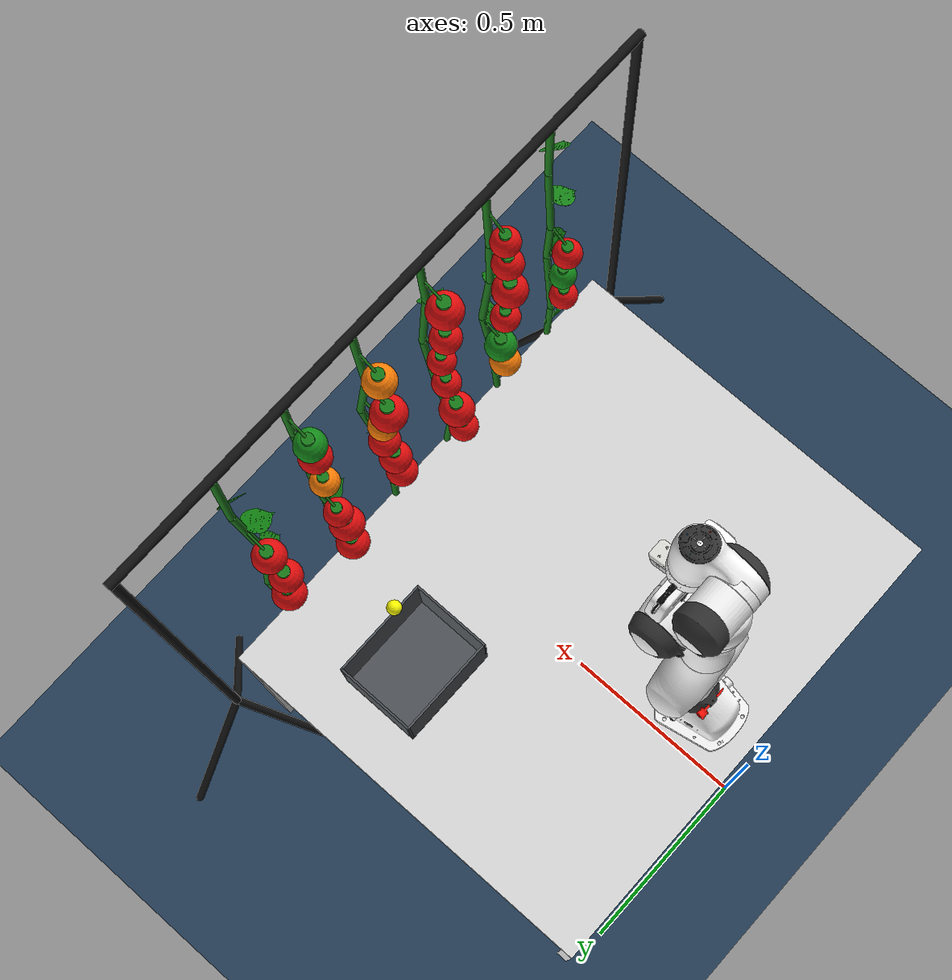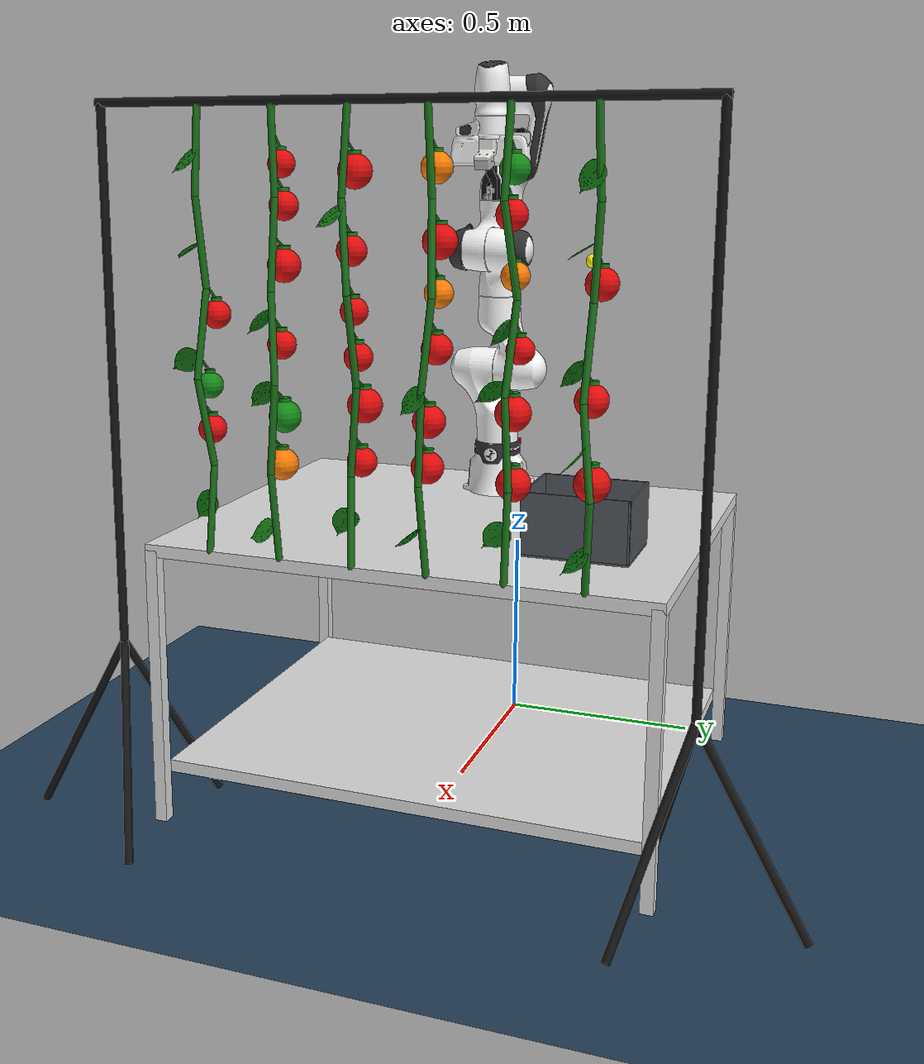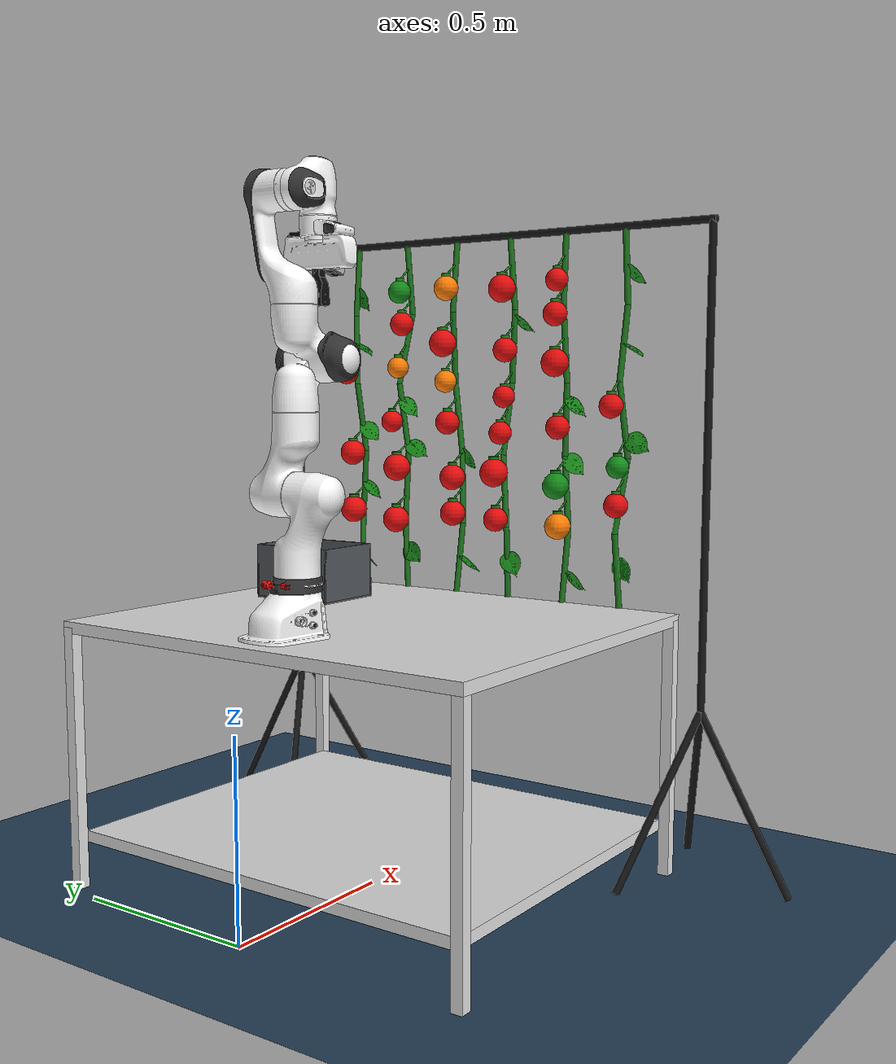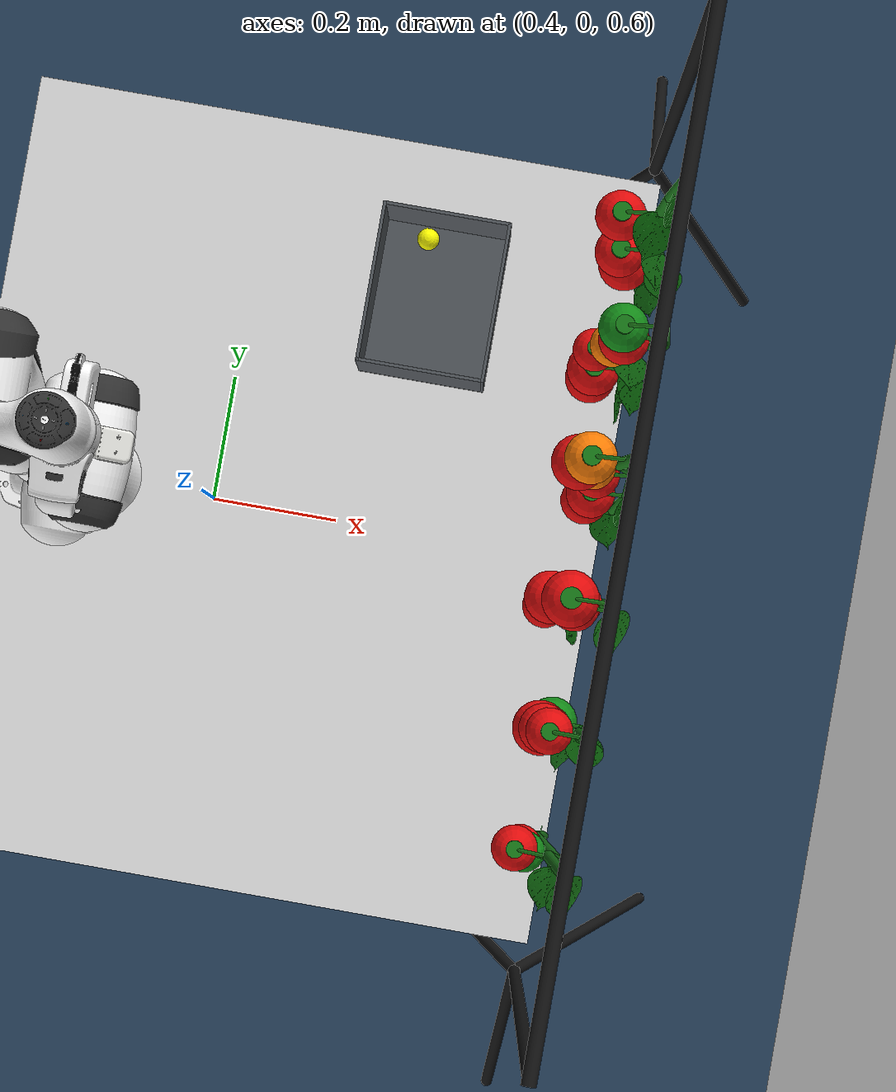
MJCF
<mujoco model="tomato_harvesting_scene">
  <!-- scene version: grasp-weld-v3 -->

  <!-- fr3.xml is in the same directory as this scene file. -->
  <include file="fr3.xml"/>

  <statistic center="0.4 0 0.5" extent="1.2"/>

  <visual>
    <headlight
      diffuse="0.6 0.6 0.6"
      ambient="0.3 0.3 0.3"
      specular="0 0 0"/>

    <rgba haze="0.15 0.25 0.35 1"/>

    <global
      azimuth="120"
      elevation="-20"/>
  </visual>

  <asset>
    <texture
      type="skybox"
      builtin="gradient"
      rgb1="0.3 0.5 0.7"
      rgb2="0 0 0"
      width="512"
      height="3072"/>

    <texture
      type="2d"
      name="groundplane"
      builtin="checker"
      mark="edge"
      rgb1="0.2 0.3 0.4"
      rgb2="0.1 0.2 0.3"
      markrgb="0.8 0.8 0.8"
      width="300"
      height="300"/>

    <material
      name="groundplane"
      texture="groundplane"
      texuniform="true"
      texrepeat="5 5"
      reflectance="0.2"/>

    <mesh
      name="tomato_leaf_mesh"
      file="tomato_plant/Leaf.stl"
      scale="0.00065 0.00065 0.00065"/>

  </asset>

  <worldbody>

    <light
      pos="0 0 3"
      dir="0 0 -1"
      directional="true"/>

    <geom
      name="floor"
      type="plane"
      size="5 5 0.1"
      material="groundplane"/>

    <!-- Harvesting table: 70 cm high, light gray -->
    <body name="table" pos="0.520091 0 0.685">

      <!--
        Tabletop:
        3 cm thick
        top surface = 0.70 m
      -->
      <geom
        name="table_top"
        type="box"
        size="0.50 0.61 0.015"
        rgba="0.88 0.88 0.88 1"/>

      <geom
        name="table_leg_1"
        type="box"
        pos="0.485 0.595 -0.3425"
        size="0.015 0.015 0.3425"
        rgba="0.88 0.88 0.88 1"/>

      <geom
        name="table_leg_2"
        type="box"
        pos="-0.485 0.595 -0.3425"
        size="0.015 0.015 0.3425"
        rgba="0.88 0.88 0.88 1"/>

      <geom
        name="table_leg_3"
        type="box"
        pos="0.485 -0.595 -0.3425"
        size="0.015 0.015 0.3425"
        rgba="0.88 0.88 0.88 1"/>

      <geom
        name="table_leg_4"
        type="box"
        pos="-0.485 -0.595 -0.3425"
        size="0.015 0.015 0.3425"
        rgba="0.88 0.88 0.88 1"/>

      <!--
        Undershelf:
      -->
      <geom
        name="table_undershelf"
        type="box"
        pos="0 0 -0.55"
        size="0.47 0.58 0.015"
        rgba="0.88 0.88 0.88 1"/>

    </body>

    <!-- Tomato support frame                                   -->
    <!-- Two ground-mounted tripod stands                       -->
    <!-- Vertical frame plane matches table back edge x=1.015182-->
    <!-- Stand centers are 7 cm outside table sides             -->
    <!-- Tripod junction height = 0.45 m                        -->
    <!-- Tripod feet are equally spaced by 120 degrees          -->
    <!-- All structural members are 20 mm diameter              -->

    <body name="tomato_support_frame">

      <!-- LEFT STAND                                           -->

      <geom
        name="support_left_vertical"
        type="cylinder"
        fromto="1.015182 0.68 0.45
                1.015182 0.68 1.70"
        size="0.01"
        rgba="0.08 0.08 0.08 1"/>

      <geom
        name="support_left_leg_1"
        type="cylinder"
        fromto="1.015182 0.68 0.45
                1.015182 0.93 0.00"
        size="0.01"
        rgba="0.08 0.08 0.08 1"/>

      <geom
        name="support_left_leg_2"
        type="cylinder"
        fromto="1.015182 0.68 0.45
                0.798676 0.555 0.00"
        size="0.01"
        rgba="0.08 0.08 0.08 1"/>

      <geom
        name="support_left_leg_3"
        type="cylinder"
        fromto="1.015182 0.68 0.45
                1.231688 0.555 0.00"
        size="0.01"
        rgba="0.08 0.08 0.08 1"/>

      <!-- RIGHT STAND                                          -->

      <geom
        name="support_right_vertical"
        type="cylinder"
        fromto="1.015182 -0.68 0.45
                1.015182 -0.68 1.70"
        size="0.01"
        rgba="0.08 0.08 0.08 1"/>

      <geom
        name="support_right_leg_1"
        type="cylinder"
        fromto="1.015182 -0.68 0.45
                1.015182 -0.93 0.00"
        size="0.01"
        rgba="0.08 0.08 0.08 1"/>

      <geom
        name="support_right_leg_2"
        type="cylinder"
        fromto="1.015182 -0.68 0.45
                1.231688 -0.555 0.00"
        size="0.01"
        rgba="0.08 0.08 0.08 1"/>

      <geom
        name="support_right_leg_3"
        type="cylinder"
        fromto="1.015182 -0.68 0.45
                0.798676 -0.555 0.00"
        size="0.01"
        rgba="0.08 0.08 0.08 1"/>

      <!-- Horizontal top support                               -->

      <geom
        name="support_top_horizontal"
        type="cylinder"
        fromto="1.015182 -0.69 1.70
                1.015182 0.69 1.70"
        size="0.01"
        rgba="0.08 0.08 0.08 1"/>

    </body>

    <!-- Vertical tomato vines                                  -->
    <!-- Main vine diameter = 16 mm                             -->
    <!-- Main vine radius   = 0.008 m                           -->
    <!-- Peduncle diameter  = 5.5 mm                            -->
    <!-- Peduncle radius    = 0.00275 m                         -->
    <!-- Vines extend from table back edge z=0.70               -->
    <!-- up to horizontal support z=1.70                        -->

    <!-- Vertical tomato vines                                  -->
    <!-- Main vine diameter = 16 mm                             -->
    <!-- Main vine radius   = 0.008 m                           -->
    <!-- Peduncle diameter  = 5.5 mm                            -->
    <!-- Peduncle radius    = 0.00275 m                         -->
    <!-- Vines extend from table back edge z=0.70               -->
    <!-- up to horizontal support z=1.70                        -->
    <!-- Each vine is made from several connected capsule       -->
    <!-- segments to create a slightly natural/wavy shape.      -->

      <!-- VINE 1: irregular S-bend                             -->

      <!-- VINE 1: irregular S-bend                             -->

      <geom name="vine_1_segment_1" type="capsule"
        fromto="1.015182 -0.439000 0.700000 0.998000 -0.431000 0.900000"
        size="0.008" rgba="0.10 0.45 0.10 1"
        contype="0" conaffinity="0"/>

      <geom name="vine_1_segment_2" type="capsule"
        fromto="0.998000 -0.431000 0.900000 1.029000 -0.450000 1.100000"
        size="0.008" rgba="0.10 0.45 0.10 1"
        contype="0" conaffinity="0"/>

      <geom name="vine_1_segment_3" type="capsule"
        fromto="1.029000 -0.450000 1.100000 1.006000 -0.434000 1.300000"
        size="0.008" rgba="0.10 0.45 0.10 1"
        contype="0" conaffinity="0"/>

      <geom name="vine_1_segment_4" type="capsule"
        fromto="1.006000 -0.434000 1.300000 1.024000 -0.445000 1.500000"
        size="0.008" rgba="0.10 0.45 0.10 1"
        contype="0" conaffinity="0"/>

      <geom name="vine_1_segment_5" type="capsule"
        fromto="1.024000 -0.445000 1.500000 1.015182 -0.439000 1.700000"
        size="0.008" rgba="0.10 0.45 0.10 1"
        contype="0" conaffinity="0"/>

      <!-- VINE 2: lower bend toward robot, straighter top      -->

      <geom name="vine_2_segment_1" type="capsule"
        fromto="1.015182 -0.263400 0.700000 1.034000 -0.270400 0.900000"
        size="0.008" rgba="0.10 0.45 0.10 1"
        contype="0" conaffinity="0"/>

      <geom name="vine_2_segment_2" type="capsule"
        fromto="1.034000 -0.270400 0.900000 1.039000 -0.254400 1.100000"
        size="0.008" rgba="0.10 0.45 0.10 1"
        contype="0" conaffinity="0"/>

      <geom name="vine_2_segment_3" type="capsule"
        fromto="1.039000 -0.254400 1.100000 1.022000 -0.267400 1.300000"
        size="0.008" rgba="0.10 0.45 0.10 1"
        contype="0" conaffinity="0"/>

      <geom name="vine_2_segment_4" type="capsule"
        fromto="1.022000 -0.267400 1.300000 1.010000 -0.260400 1.500000"
        size="0.008" rgba="0.10 0.45 0.10 1"
        contype="0" conaffinity="0"/>

      <geom name="vine_2_segment_5" type="capsule"
        fromto="1.010000 -0.260400 1.500000 1.015182 -0.263400 1.700000"
        size="0.008" rgba="0.10 0.45 0.10 1"
        contype="0" conaffinity="0"/>

      <!-- VINE 3: pronounced asymmetric S                      -->

      <geom name="vine_3_segment_1" type="capsule"
        fromto="1.015182 -0.087800 0.700000 0.993000 -0.095800 0.900000"
        size="0.008" rgba="0.10 0.45 0.10 1"
        contype="0" conaffinity="0"/>

      <geom name="vine_3_segment_2" type="capsule"
        fromto="0.993000 -0.095800 0.900000 1.004000 -0.076800 1.100000"
        size="0.008" rgba="0.10 0.45 0.10 1"
        contype="0" conaffinity="0"/>

      <geom name="vine_3_segment_3" type="capsule"
        fromto="1.004000 -0.076800 1.100000 1.037000 -0.083800 1.300000"
        size="0.008" rgba="0.10 0.45 0.10 1"
        contype="0" conaffinity="0"/>

      <geom name="vine_3_segment_4" type="capsule"
        fromto="1.037000 -0.083800 1.300000 1.025000 -0.098800 1.500000"
        size="0.008" rgba="0.10 0.45 0.10 1"
        contype="0" conaffinity="0"/>

      <geom name="vine_3_segment_5" type="capsule"
        fromto="1.025000 -0.098800 1.500000 1.015182 -0.087800 1.700000"
        size="0.008" rgba="0.10 0.45 0.10 1"
        contype="0" conaffinity="0"/>

      <!-- VINE 4: broad bow with small upper kink              -->

      <geom name="vine_4_segment_1" type="capsule"
        fromto="1.015182 0.087800 0.700000 1.027000 0.073800 0.900000"
        size="0.008" rgba="0.10 0.45 0.10 1"
        contype="0" conaffinity="0"/>

      <geom name="vine_4_segment_2" type="capsule"
        fromto="1.027000 0.073800 0.900000 1.036000 0.082800 1.100000"
        size="0.008" rgba="0.10 0.45 0.10 1"
        contype="0" conaffinity="0"/>

      <geom name="vine_4_segment_3" type="capsule"
        fromto="1.036000 0.082800 1.100000 1.031000 0.103800 1.300000"
        size="0.008" rgba="0.10 0.45 0.10 1"
        contype="0" conaffinity="0"/>

      <geom name="vine_4_segment_4" type="capsule"
        fromto="1.031000 0.103800 1.300000 1.001000 0.092800 1.500000"
        size="0.008" rgba="0.10 0.45 0.10 1"
        contype="0" conaffinity="0"/>

      <geom name="vine_4_segment_5" type="capsule"
        fromto="1.001000 0.092800 1.500000 1.015182 0.087800 1.700000"
        size="0.008" rgba="0.10 0.45 0.10 1"
        contype="0" conaffinity="0"/>

      <!-- VINE 5: relatively straight lower half, wavy upper   -->

      <geom name="vine_5_segment_1" type="capsule"
        fromto="1.015182 0.263400 0.700000 1.009000 0.267400 0.900000"
        size="0.008" rgba="0.10 0.45 0.10 1"
        contype="0" conaffinity="0"/>

      <geom name="vine_5_segment_2" type="capsule"
        fromto="1.009000 0.267400 0.900000 1.013000 0.258400 1.100000"
        size="0.008" rgba="0.10 0.45 0.10 1"
        contype="0" conaffinity="0"/>

      <geom name="vine_5_segment_3" type="capsule"
        fromto="1.013000 0.258400 1.100000 0.992000 0.275400 1.300000"
        size="0.008" rgba="0.10 0.45 0.10 1"
        contype="0" conaffinity="0"/>

      <geom name="vine_5_segment_4" type="capsule"
        fromto="0.992000 0.275400 1.300000 1.031000 0.256400 1.500000"
        size="0.008" rgba="0.10 0.45 0.10 1"
        contype="0" conaffinity="0"/>

      <geom name="vine_5_segment_5" type="capsule"
        fromto="1.031000 0.256400 1.500000 1.015182 0.263400 1.700000"
        size="0.008" rgba="0.10 0.45 0.10 1"
        contype="0" conaffinity="0"/>

      <!-- VINE 6: stronger lower S, gentle upper return        -->

      <geom name="vine_6_segment_1" type="capsule"
        fromto="1.015182 0.439000 0.700000 1.038000 0.449000 0.900000"
        size="0.008" rgba="0.10 0.45 0.10 1"
        contype="0" conaffinity="0"/>

      <geom name="vine_6_segment_2" type="capsule"
        fromto="1.038000 0.449000 0.900000 1.025000 0.427000 1.100000"
        size="0.008" rgba="0.10 0.45 0.10 1"
        contype="0" conaffinity="0"/>

      <geom name="vine_6_segment_3" type="capsule"
        fromto="1.025000 0.427000 1.100000 0.995000 0.435000 1.300000"
        size="0.008" rgba="0.10 0.45 0.10 1"
        contype="0" conaffinity="0"/>

      <geom name="vine_6_segment_4" type="capsule"
        fromto="0.995000 0.435000 1.300000 1.007000 0.447000 1.500000"
        size="0.008" rgba="0.10 0.45 0.10 1"
        contype="0" conaffinity="0"/>

      <geom name="vine_6_segment_5" type="capsule"
        fromto="1.007000 0.447000 1.500000 1.015182 0.439000 1.700000"
        size="0.008" rgba="0.10 0.45 0.10 1"
        contype="0" conaffinity="0"/>

      <!-- GENERATED RANDOM VINE LEAVES: START -->

      <!-- Leaf 1, vine 1 -->

      <geom
        name="vine_1_leaf_1"
        type="mesh"
        mesh="tomato_leaf_mesh"
        pos="1.005336 -0.425877 0.831331"
        euler="-0.740592 0.000000 1.390287"
        rgba="0.0302 0.4502 0.0302 1"
        contype="0"
        conaffinity="0"/>

      <!-- Leaf 2, vine 1 -->

      <geom
        name="vine_1_leaf_2"
        type="mesh"
        mesh="tomato_leaf_mesh"
        pos="1.007167 -0.439998 1.401741"
        euler="-1.027292 0.000000 3.191927"
        rgba="0.0859 0.5059 0.0859 1"
        contype="0"
        conaffinity="0"/>

      <!-- Leaf 3, vine 1 -->

      <geom
        name="vine_1_leaf_3"
        type="mesh"
        mesh="tomato_leaf_mesh"
        pos="1.025718 -0.436807 1.597715"
        euler="-0.929719 0.000000 0.717692"
        rgba="0.1017 0.5217 0.1017 1"
        contype="0"
        conaffinity="0"/>

      <!-- Leaf 4, vine 1 -->

      <geom
        name="vine_1_leaf_4"
        type="mesh"
        mesh="tomato_leaf_mesh"
        pos="1.025301 -0.451954 1.164277"
        euler="-0.862620 0.000000 5.192239"
        rgba="0.0759 0.4959 0.0759 1"
        contype="0"
        conaffinity="0"/>

      <!-- Leaf 5, vine 2 -->

      <geom
        name="vine_2_leaf_5"
        type="mesh"
        mesh="tomato_leaf_mesh"
        pos="1.017660 -0.272295 0.782470"
        euler="-0.926899 0.000000 3.991350"
        rgba="0.1139 0.5339 0.1139 1"
        contype="0"
        conaffinity="0"/>

      <!-- Leaf 6, vine 2 -->

      <geom
        name="vine_2_leaf_6"
        type="mesh"
        mesh="tomato_leaf_mesh"
        pos="1.044465 -0.260014 1.108751"
        euler="-0.635900 0.000000 5.600870"
        rgba="0.0875 0.5075 0.0875 1"
        contype="0"
        conaffinity="0"/>

      <!-- Leaf 7, vine 2 -->

      <geom
        name="vine_2_leaf_7"
        type="mesh"
        mesh="tomato_leaf_mesh"
        pos="1.032719 -0.267083 1.265186"
        euler="-0.708047 0.000000 6.037449"
        rgba="0.0707 0.4907 0.0707 1"
        contype="0"
        conaffinity="0"/>

      <!-- Leaf 8, vine 3 -->

      <geom
        name="vine_3_leaf_8"
        type="mesh"
        mesh="tomato_leaf_mesh"
        pos="0.997902 -0.085566 0.825027"
        euler="-0.678126 0.000000 2.011651"
        rgba="0.0852 0.5052 0.0852 1"
        contype="0"
        conaffinity="0"/>

      <!-- Leaf 9, vine 3 -->

      <geom
        name="vine_3_leaf_9"
        type="mesh"
        mesh="tomato_leaf_mesh"
        pos="1.032473 -0.092358 1.480150"
        euler="-1.022590 0.000000 0.667731"
        rgba="0.0993 0.5193 0.0993 1"
        contype="0"
        conaffinity="0"/>

      <!-- Leaf 10, vine 4 -->

      <geom
        name="vine_4_leaf_10"
        type="mesh"
        mesh="tomato_leaf_mesh"
        pos="1.029290 0.081974 0.806101"
        euler="-0.943449 0.000000 0.201481"
        rgba="0.0750 0.4950 0.0750 1"
        contype="0"
        conaffinity="0"/>

      <!-- Leaf 11, vine 4 -->

      <geom
        name="vine_4_leaf_11"
        type="mesh"
        mesh="tomato_leaf_mesh"
        pos="1.040252 0.090396 1.109241"
        euler="-0.799540 0.000000 0.975930"
        rgba="0.0668 0.4868 0.0668 1"
        contype="0"
        conaffinity="0"/>

      <!-- Leaf 12, vine 5 -->

      <geom
        name="vine_5_leaf_12"
        type="mesh"
        mesh="tomato_leaf_mesh"
        pos="1.010236 0.273726 0.820910"
        euler="-0.991900 0.000000 1.722435"
        rgba="0.0890 0.5090 0.0890 1"
        contype="0"
        conaffinity="0"/>

      <!-- Leaf 13, vine 5 -->

      <geom
        name="vine_5_leaf_13"
        type="mesh"
        mesh="tomato_leaf_mesh"
        pos="1.015624 0.256409 1.134842"
        euler="-0.854213 0.000000 5.615659"
        rgba="0.0645 0.4845 0.0645 1"
        contype="0"
        conaffinity="0"/>

      <!-- Leaf 14, vine 5 -->

      <geom
        name="vine_5_leaf_14"
        type="mesh"
        mesh="tomato_leaf_mesh"
        pos="1.003285 0.269372 1.263449"
        euler="-0.628022 0.000000 5.909350"
        rgba="0.0823 0.5023 0.0823 1"
        contype="0"
        conaffinity="0"/>

      <!-- Leaf 15, vine 6 -->

      <geom
        name="vine_6_leaf_15"
        type="mesh"
        mesh="tomato_leaf_mesh"
        pos="1.018628 0.426306 1.187841"
        euler="-0.670745 0.000000 5.729369"
        rgba="0.0813 0.5013 0.0813 1"
        contype="0"
        conaffinity="0"/>

      <!-- Leaf 16, vine 6 -->

      <geom
        name="vine_6_leaf_16"
        type="mesh"
        mesh="tomato_leaf_mesh"
        pos="1.032718 0.448089 0.794839"
        euler="-0.854927 0.000000 0.574417"
        rgba="0.0808 0.5008 0.0808 1"
        contype="0"
        conaffinity="0"/>

      <!-- Leaf 17, vine 6 -->

      <geom
        name="vine_6_leaf_17"
        type="mesh"
        mesh="tomato_leaf_mesh"
        pos="0.994303 0.441800 1.421465"
        euler="-1.029851 0.000000 3.202561"
        rgba="0.0529 0.4729 0.0529 1"
        contype="0"
        conaffinity="0"/>

      <!-- Leaf 18, vine 6 -->

      <geom
        name="vine_6_leaf_18"
        type="mesh"
        mesh="tomato_leaf_mesh"
        pos="1.013034 0.451443 1.574451"
        euler="-0.732224 0.000000 1.187967"
        rgba="0.0669 0.4869 0.0669 1"
        contype="0"
        conaffinity="0"/>

      <!-- Leaf 19, vine 6 -->

      <geom
        name="vine_6_leaf_19"
        type="mesh"
        mesh="tomato_leaf_mesh"
        pos="1.038712 0.436353 1.012025"
        euler="-0.709574 0.000000 6.242602"
        rgba="0.0673 0.4873 0.0673 1"
        contype="0"
        conaffinity="0"/>
      <!-- GENERATED RANDOM VINE LEAVES: END -->

    <!-- GENERATED MULTI-TOMATO SCENE                            -->
    <!-- 30 tomatoes: 3 on outer vines, 6 on inner vines -->

    <!-- Tomato 1: vine 3, red,
         diameter=6.37 cm -->

    <body
      name="tomato_1_stem_tip"
      pos="0.979773 -0.081435 1.193991">

      <!--
        Peduncle length = 6.0 cm.
        From vine toward tomato it slopes downward
        39.8 degrees.
      -->

      <geom
        name="tomato_1_peduncle"
        type="capsule"
        fromto="0 0 0
                0.046077
                0.000000
                0.038431"
        size="0.00275"
        rgba="0.12 0.50 0.10 1"
        contype="0"
        conaffinity="0"/>

    </body>

    <body
      name="tomato_1"
      pos="0.979773 -0.081435 1.162126">

      <freejoint
        name="tomato_1_freejoint"/>

      <geom
        name="tomato_1_geom"
        type="sphere"
        size="0.031864"
        mass="0.050552"
        friction="1.5 0.02 0.002"
        solref="0.01 1"
        condim="4"
        rgba="0.90 0.05 0.05 1"/>

      <geom
        name="tomato_1_calyx"
        type="cylinder"
        pos="0 0 0.033864"
        size="0.011949 0.004"
        rgba="0.10 0.50 0.10 1"
        contype="0"
        conaffinity="0"/>

      <site
        name="tomato_1_target_site"
        pos="0 0 0"
        type="sphere"
        size="0.004"
        rgba="0 1 0 0"/>

    </body>

    <!-- Tomato 2: vine 3, red,
         diameter=7.48 cm -->

    <body
      name="tomato_2_stem_tip"
      pos="0.967252 -0.092092 1.591617">

      <!--
        Peduncle length = 6.0 cm.
        From vine toward tomato it slopes downward
        30.4 degrees.
      -->

      <geom
        name="tomato_2_peduncle"
        type="capsule"
        fromto="0 0 0
                0.051760
                0.000000
                0.030346"
        size="0.00275"
        rgba="0.12 0.50 0.10 1"
        contype="0"
        conaffinity="0"/>

    </body>

    <body
      name="tomato_2"
      pos="0.967252 -0.092092 1.554195">

      <freejoint
        name="tomato_2_freejoint"/>

      <geom
        name="tomato_2_geom"
        type="sphere"
        size="0.037422"
        mass="0.081887"
        friction="1.5 0.02 0.002"
        solref="0.01 1"
        condim="4"
        rgba="0.90 0.05 0.05 1"/>

      <geom
        name="tomato_2_calyx"
        type="cylinder"
        pos="0 0 0.039422"
        size="0.014033 0.004"
        rgba="0.10 0.50 0.10 1"
        contype="0"
        conaffinity="0"/>

      <site
        name="tomato_2_target_site"
        pos="0 0 0"
        type="sphere"
        size="0.004"
        rgba="0 1 0 0"/>

    </body>

    <!-- Tomato 3: vine 3, red,
         diameter=7.83 cm -->

    <body
      name="tomato_3_stem_tip"
      pos="0.953994 -0.077484 1.091851">

      <!--
        Peduncle length = 6.0 cm.
        From vine toward tomato it slopes downward
        27.5 degrees.
      -->

      <geom
        name="tomato_3_peduncle"
        type="capsule"
        fromto="0 0 0
                0.053230
                0.000000
                0.027687"
        size="0.00275"
        rgba="0.12 0.50 0.10 1"
        contype="0"
        conaffinity="0"/>

    </body>

    <body
      name="tomato_3"
      pos="0.953994 -0.077484 1.052722">

      <freejoint
        name="tomato_3_freejoint"/>

      <geom
        name="tomato_3_geom"
        type="sphere"
        size="0.039129"
        mass="0.093610"
        friction="1.5 0.02 0.002"
        solref="0.01 1"
        condim="4"
        rgba="0.90 0.05 0.05 1"/>

      <geom
        name="tomato_3_calyx"
        type="cylinder"
        pos="0 0 0.041129"
        size="0.014673 0.004"
        rgba="0.10 0.50 0.10 1"
        contype="0"
        conaffinity="0"/>

      <site
        name="tomato_3_target_site"
        pos="0 0 0"
        type="sphere"
        size="0.004"
        rgba="0 1 0 0"/>

    </body>

    <!-- Tomato 4: vine 3, red,
         diameter=6.76 cm -->

    <body
      name="tomato_4_stem_tip"
      pos="0.949953 -0.086879 0.958192">

      <!--
        Peduncle length = 6.0 cm.
        From vine toward tomato it slopes downward
        36.5 degrees.
      -->

      <geom
        name="tomato_4_peduncle"
        type="capsule"
        fromto="0 0 0
                0.048212
                0.000000
                0.035716"
        size="0.00275"
        rgba="0.12 0.50 0.10 1"
        contype="0"
        conaffinity="0"/>

    </body>

    <body
      name="tomato_4"
      pos="0.949953 -0.086879 0.924387">

      <freejoint
        name="tomato_4_freejoint"/>

      <geom
        name="tomato_4_geom"
        type="sphere"
        size="0.033805"
        mass="0.060361"
        friction="1.5 0.02 0.002"
        solref="0.01 1"
        condim="4"
        rgba="0.90 0.05 0.05 1"/>

      <geom
        name="tomato_4_calyx"
        type="cylinder"
        pos="0 0 0.035805"
        size="0.012677 0.004"
        rgba="0.10 0.50 0.10 1"
        contype="0"
        conaffinity="0"/>

      <site
        name="tomato_4_target_site"
        pos="0 0 0"
        type="sphere"
        size="0.004"
        rgba="0 1 0 0"/>

    </body>

    <!-- Tomato 5: vine 3, red,
         diameter=6.70 cm -->

    <body
      name="tomato_5_stem_tip"
      pos="0.979592 -0.095711 1.422650">

      <!--
        Peduncle length = 6.0 cm.
        From vine toward tomato it slopes downward
        37.1 degrees.
      -->

      <geom
        name="tomato_5_peduncle"
        type="capsule"
        fromto="0 0 0
                0.047879
                0.000000
                0.036161"
        size="0.00275"
        rgba="0.12 0.50 0.10 1"
        contype="0"
        conaffinity="0"/>

    </body>

    <body
      name="tomato_5"
      pos="0.979592 -0.095711 1.389157">

      <freejoint
        name="tomato_5_freejoint"/>

      <geom
        name="tomato_5_geom"
        type="sphere"
        size="0.033493"
        mass="0.058706"
        friction="1.5 0.02 0.002"
        solref="0.01 1"
        condim="4"
        rgba="0.90 0.05 0.05 1"/>

      <geom
        name="tomato_5_calyx"
        type="cylinder"
        pos="0 0 0.035493"
        size="0.012560 0.004"
        rgba="0.10 0.50 0.10 1"
        contype="0"
        conaffinity="0"/>

      <site
        name="tomato_5_target_site"
        pos="0 0 0"
        type="sphere"
        size="0.004"
        rgba="0 1 0 0"/>

    </body>

    <!-- Tomato 6: vine 3, red,
         diameter=6.13 cm -->

    <body
      name="tomato_6_stem_tip"
      pos="0.990385 -0.086231 1.292358">

      <!--
        Peduncle length = 6.0 cm.
        From vine toward tomato it slopes downward
        41.9 degrees.
      -->

      <geom
        name="tomato_6_peduncle"
        type="capsule"
        fromto="0 0 0
                0.044671
                0.000000
                0.040057"
        size="0.00275"
        rgba="0.12 0.50 0.10 1"
        contype="0"
        conaffinity="0"/>

    </body>

    <body
      name="tomato_6"
      pos="0.990385 -0.086231 1.261701">

      <freejoint
        name="tomato_6_freejoint"/>

      <geom
        name="tomato_6_geom"
        type="sphere"
        size="0.030657"
        mass="0.045021"
        friction="1.5 0.02 0.002"
        solref="0.01 1"
        condim="4"
        rgba="0.90 0.05 0.05 1"/>

      <geom
        name="tomato_6_calyx"
        type="cylinder"
        pos="0 0 0.032657"
        size="0.011496 0.004"
        rgba="0.10 0.50 0.10 1"
        contype="0"
        conaffinity="0"/>

      <site
        name="tomato_6_target_site"
        pos="0 0 0"
        type="sphere"
        size="0.004"
        rgba="0 1 0 0"/>

    </body>

    <!-- Tomato 7: vine 1, red,
         diameter=6.48 cm -->

    <body
      name="tomato_7_stem_tip"
      pos="0.960085 -0.434453 1.270505">

      <!--
        Peduncle length = 6.0 cm.
        From vine toward tomato it slopes downward
        39.0 degrees.
      -->

      <geom
        name="tomato_7_peduncle"
        type="capsule"
        fromto="0 0 0
                0.046656
                0.000000
                0.037726"
        size="0.00275"
        rgba="0.12 0.50 0.10 1"
        contype="0"
        conaffinity="0"/>

    </body>

    <body
      name="tomato_7"
      pos="0.960085 -0.434453 1.238128">

      <freejoint
        name="tomato_7_freejoint"/>

      <geom
        name="tomato_7_geom"
        type="sphere"
        size="0.032377"
        mass="0.053032"
        friction="1.5 0.02 0.002"
        solref="0.01 1"
        condim="4"
        rgba="0.90 0.05 0.05 1"/>

      <geom
        name="tomato_7_calyx"
        type="cylinder"
        pos="0 0 0.034377"
        size="0.012141 0.004"
        rgba="0.10 0.50 0.10 1"
        contype="0"
        conaffinity="0"/>

      <site
        name="tomato_7_target_site"
        pos="0 0 0"
        type="sphere"
        size="0.004"
        rgba="0 1 0 0"/>

    </body>

    <!-- Tomato 8: vine 1, green,
         diameter=6.06 cm -->

    <body
      name="tomato_8_stem_tip"
      pos="0.978990 -0.445999 1.109500">

      <!--
        Peduncle length = 6.0 cm.
        From vine toward tomato it slopes downward
        42.5 degrees.
      -->

      <geom
        name="tomato_8_peduncle"
        type="capsule"
        fromto="0 0 0
                0.044259
                0.000000
                0.040511"
        size="0.00275"
        rgba="0.12 0.50 0.10 1"
        contype="0"
        conaffinity="0"/>

    </body>

    <body
      name="tomato_8"
      pos="0.978990 -0.445999 1.079187">

      <freejoint
        name="tomato_8_freejoint"/>

      <geom
        name="tomato_8_geom"
        type="sphere"
        size="0.030313"
        mass="0.043520"
        friction="1.5 0.02 0.002"
        solref="0.015 1"
        solimp="0.85 0.98 0.0012 0.5 2"
        condim="4"
        rgba="0.08 0.55 0.10 1"/>

      <geom
        name="tomato_8_calyx"
        type="cylinder"
        pos="0 0 0.032313"
        size="0.011367 0.004"
        rgba="0.10 0.50 0.10 1"
        contype="0"
        conaffinity="0"/>

      <site
        name="tomato_8_target_site"
        pos="0 0 0"
        type="sphere"
        size="0.004"
        rgba="0 1 0 0"/>

    </body>

    <!-- Tomato 9: vine 1, red,
         diameter=6.49 cm -->

    <body
      name="tomato_9_stem_tip"
      pos="0.974227 -0.445079 1.010584">

      <!--
        Peduncle length = 6.0 cm.
        From vine toward tomato it slopes downward
        38.8 degrees.
      -->

      <geom
        name="tomato_9_peduncle"
        type="capsule"
        fromto="0 0 0
                0.046744
                0.000000
                0.037617"
        size="0.00275"
        rgba="0.12 0.50 0.10 1"
        contype="0"
        conaffinity="0"/>

    </body>

    <body
      name="tomato_9"
      pos="0.974227 -0.445079 0.978128">

      <freejoint
        name="tomato_9_freejoint"/>

      <geom
        name="tomato_9_geom"
        type="sphere"
        size="0.032456"
        mass="0.053420"
        friction="1.5 0.02 0.002"
        solref="0.01 1"
        condim="4"
        rgba="0.90 0.05 0.05 1"/>

      <geom
        name="tomato_9_calyx"
        type="cylinder"
        pos="0 0 0.034456"
        size="0.012171 0.004"
        rgba="0.10 0.50 0.10 1"
        contype="0"
        conaffinity="0"/>

      <site
        name="tomato_9_target_site"
        pos="0 0 0"
        type="sphere"
        size="0.004"
        rgba="0 1 0 0"/>

    </body>

    <!-- Tomato 10: vine 2, red,
         diameter=6.52 cm -->

    <body
      name="tomato_10_stem_tip"
      pos="0.979333 -0.264154 1.212649">

      <!--
        Peduncle length = 6.0 cm.
        From vine toward tomato it slopes downward
        38.6 degrees.
      -->

      <geom
        name="tomato_10_peduncle"
        type="capsule"
        fromto="0 0 0
                0.046912
                0.000000
                0.037406"
        size="0.00275"
        rgba="0.12 0.50 0.10 1"
        contype="0"
        conaffinity="0"/>

    </body>

    <body
      name="tomato_10"
      pos="0.979333 -0.264154 1.180042">

      <freejoint
        name="tomato_10_freejoint"/>

      <geom
        name="tomato_10_geom"
        type="sphere"
        size="0.032607"
        mass="0.054170"
        friction="1.5 0.02 0.002"
        solref="0.01 1"
        condim="4"
        rgba="0.90 0.05 0.05 1"/>

      <geom
        name="tomato_10_calyx"
        type="cylinder"
        pos="0 0 0.034607"
        size="0.012228 0.004"
        rgba="0.10 0.50 0.10 1"
        contype="0"
        conaffinity="0"/>

      <site
        name="tomato_10_target_site"
        pos="0 0 0"
        type="sphere"
        size="0.004"
        rgba="0 1 0 0"/>

    </body>

    <!-- Tomato 11: vine 2, green,
         diameter=7.26 cm -->

    <body
      name="tomato_11_stem_tip"
      pos="0.988043 -0.255177 1.058230">

      <!--
        Peduncle length = 6.0 cm.
        From vine toward tomato it slopes downward
        32.3 degrees.
      -->

      <geom
        name="tomato_11_peduncle"
        type="capsule"
        fromto="0 0 0
                0.050714
                0.000000
                0.032063"
        size="0.00275"
        rgba="0.12 0.50 0.10 1"
        contype="0"
        conaffinity="0"/>

    </body>

    <body
      name="tomato_11"
      pos="0.988043 -0.255177 1.021937">

      <freejoint
        name="tomato_11_freejoint"/>

      <geom
        name="tomato_11_geom"
        type="sphere"
        size="0.036293"
        mass="0.074692"
        friction="1.5 0.02 0.002"
        solref="0.015 1"
        solimp="0.85 0.98 0.0012 0.5 2"
        condim="4"
        rgba="0.08 0.55 0.10 1"/>

      <geom
        name="tomato_11_calyx"
        type="cylinder"
        pos="0 0 0.038293"
        size="0.013610 0.004"
        rgba="0.10 0.50 0.10 1"
        contype="0"
        conaffinity="0"/>

      <site
        name="tomato_11_target_site"
        pos="0 0 0"
        type="sphere"
        size="0.004"
        rgba="0 1 0 0"/>

    </body>

    <!-- Tomato 12: vine 2, red,
         diameter=7.51 cm -->

    <body
      name="tomato_12_stem_tip"
      pos="0.962934 -0.263212 1.389521">

      <!--
        Peduncle length = 6.0 cm.
        From vine toward tomato it slopes downward
        30.1 degrees.
      -->

      <geom
        name="tomato_12_peduncle"
        type="capsule"
        fromto="0 0 0
                0.051887
                0.000000
                0.030129"
        size="0.00275"
        rgba="0.12 0.50 0.10 1"
        contype="0"
        conaffinity="0"/>

    </body>

    <body
      name="tomato_12"
      pos="0.962934 -0.263212 1.351958">

      <freejoint
        name="tomato_12_freejoint"/>

      <geom
        name="tomato_12_geom"
        type="sphere"
        size="0.037564"
        mass="0.082818"
        friction="1.5 0.02 0.002"
        solref="0.01 1"
        condim="4"
        rgba="0.90 0.05 0.05 1"/>

      <geom
        name="tomato_12_calyx"
        type="cylinder"
        pos="0 0 0.039564"
        size="0.014086 0.004"
        rgba="0.10 0.50 0.10 1"
        contype="0"
        conaffinity="0"/>

      <site
        name="tomato_12_target_site"
        pos="0 0 0"
        type="sphere"
        size="0.004"
        rgba="0 1 0 0"/>

    </body>

    <!-- Tomato 13: vine 2, red,
         diameter=6.55 cm -->

    <body
      name="tomato_13_stem_tip"
      pos="0.964223 -0.261160 1.513468">

      <!--
        Peduncle length = 6.0 cm.
        From vine toward tomato it slopes downward
        38.3 degrees.
      -->

      <geom
        name="tomato_13_peduncle"
        type="capsule"
        fromto="0 0 0
                0.047089
                0.000000
                0.037184"
        size="0.00275"
        rgba="0.12 0.50 0.10 1"
        contype="0"
        conaffinity="0"/>

    </body>

    <body
      name="tomato_13"
      pos="0.964223 -0.261160 1.480701">

      <freejoint
        name="tomato_13_freejoint"/>

      <geom
        name="tomato_13_geom"
        type="sphere"
        size="0.032767"
        mass="0.054971"
        friction="1.5 0.02 0.002"
        solref="0.01 1"
        condim="4"
        rgba="0.90 0.05 0.05 1"/>

      <geom
        name="tomato_13_calyx"
        type="cylinder"
        pos="0 0 0.034767"
        size="0.012288 0.004"
        rgba="0.10 0.50 0.10 1"
        contype="0"
        conaffinity="0"/>

      <site
        name="tomato_13_target_site"
        pos="0 0 0"
        type="sphere"
        size="0.004"
        rgba="0 1 0 0"/>

    </body>

    <!-- Tomato 14: vine 2, orange,
         diameter=7.18 cm -->

    <body
      name="tomato_14_stem_tip"
      pos="0.985703 -0.263892 0.948682">

      <!--
        Peduncle length = 6.0 cm.
        From vine toward tomato it slopes downward
        33.0 degrees.
      -->

      <geom
        name="tomato_14_peduncle"
        type="capsule"
        fromto="0 0 0
                0.050331
                0.000000
                0.032662"
        size="0.00275"
        rgba="0.12 0.50 0.10 1"
        contype="0"
        conaffinity="0"/>

    </body>

    <body
      name="tomato_14"
      pos="0.985703 -0.263892 0.912789">

      <freejoint
        name="tomato_14_freejoint"/>

      <geom
        name="tomato_14_geom"
        type="sphere"
        size="0.035893"
        mass="0.072253"
        friction="1.5 0.02 0.002"
        solref="0.020 1"
        solimp="0.78 0.96 0.0017 0.5 2"
        condim="4"
        rgba="1.00 0.50 0.02 1"/>

      <geom
        name="tomato_14_calyx"
        type="cylinder"
        pos="0 0 0.037893"
        size="0.013460 0.004"
        rgba="0.10 0.50 0.10 1"
        contype="0"
        conaffinity="0"/>

      <site
        name="tomato_14_target_site"
        pos="0 0 0"
        type="sphere"
        size="0.004"
        rgba="0 1 0 0"/>

    </body>

    <!-- Tomato 15: vine 2, red,
         diameter=6.07 cm -->

    <body
      name="tomato_15_stem_tip"
      pos="0.969346 -0.262504 1.599812">

      <!--
        Peduncle length = 6.0 cm.
        From vine toward tomato it slopes downward
        42.4 degrees.
      -->

      <geom
        name="tomato_15_peduncle"
        type="capsule"
        fromto="0 0 0
                0.044289
                0.000000
                0.040478"
        size="0.00275"
        rgba="0.12 0.50 0.10 1"
        contype="0"
        conaffinity="0"/>

    </body>

    <body
      name="tomato_15"
      pos="0.969346 -0.262504 1.569474">

      <freejoint
        name="tomato_15_freejoint"/>

      <geom
        name="tomato_15_geom"
        type="sphere"
        size="0.030338"
        mass="0.043630"
        friction="1.5 0.02 0.002"
        solref="0.01 1"
        condim="4"
        rgba="0.90 0.05 0.05 1"/>

      <geom
        name="tomato_15_calyx"
        type="cylinder"
        pos="0 0 0.032338"
        size="0.011377 0.004"
        rgba="0.10 0.50 0.10 1"
        contype="0"
        conaffinity="0"/>

      <site
        name="tomato_15_target_site"
        pos="0 0 0"
        type="sphere"
        size="0.004"
        rgba="0 1 0 0"/>

    </body>

    <!-- Tomato 16: vine 4, orange,
         diameter=6.83 cm -->

    <body
      name="tomato_16_stem_tip"
      pos="0.961784 0.089491 1.597160">

      <!--
        Peduncle length = 6.0 cm.
        From vine toward tomato it slopes downward
        35.9 degrees.
      -->

      <geom
        name="tomato_16_peduncle"
        type="capsule"
        fromto="0 0 0
                0.048601
                0.000000
                0.035185"
        size="0.00275"
        rgba="0.12 0.50 0.10 1"
        contype="0"
        conaffinity="0"/>

    </body>

    <body
      name="tomato_16"
      pos="0.961784 0.089491 1.562986">

      <freejoint
        name="tomato_16_freejoint"/>

      <geom
        name="tomato_16_geom"
        type="sphere"
        size="0.034175"
        mass="0.062364"
        friction="1.5 0.02 0.002"
        solref="0.020 1"
        solimp="0.78 0.96 0.0017 0.5 2"
        condim="4"
        rgba="1.00 0.50 0.02 1"/>

      <geom
        name="tomato_16_calyx"
        type="cylinder"
        pos="0 0 0.036175"
        size="0.012816 0.004"
        rgba="0.10 0.50 0.10 1"
        contype="0"
        conaffinity="0"/>

      <site
        name="tomato_16_target_site"
        pos="0 0 0"
        type="sphere"
        size="0.004"
        rgba="0 1 0 0"/>

    </body>

    <!-- Tomato 17: vine 4, red,
         diameter=7.19 cm -->

    <body
      name="tomato_17_stem_tip"
      pos="0.981128 0.078295 0.967277">

      <!--
        Peduncle length = 6.0 cm.
        From vine toward tomato it slopes downward
        32.9 degrees.
      -->

      <geom
        name="tomato_17_peduncle"
        type="capsule"
        fromto="0 0 0
                0.050367
                0.000000
                0.032607"
        size="0.00275"
        rgba="0.12 0.50 0.10 1"
        contype="0"
        conaffinity="0"/>

    </body>

    <body
      name="tomato_17"
      pos="0.981128 0.078295 0.931346">

      <freejoint
        name="tomato_17_freejoint"/>

      <geom
        name="tomato_17_geom"
        type="sphere"
        size="0.035930"
        mass="0.072478"
        friction="1.5 0.02 0.002"
        solref="0.01 1"
        condim="4"
        rgba="0.90 0.05 0.05 1"/>

      <geom
        name="tomato_17_calyx"
        type="cylinder"
        pos="0 0 0.037930"
        size="0.013474 0.004"
        rgba="0.10 0.50 0.10 1"
        contype="0"
        conaffinity="0"/>

      <site
        name="tomato_17_target_site"
        pos="0 0 0"
        type="sphere"
        size="0.004"
        rgba="0 1 0 0"/>

    </body>

    <!-- Tomato 18: vine 4, red,
         diameter=6.79 cm -->

    <body
      name="tomato_18_stem_tip"
      pos="0.983696 0.099454 1.223063">

      <!--
        Peduncle length = 6.0 cm.
        From vine toward tomato it slopes downward
        36.3 degrees.
      -->

      <geom
        name="tomato_18_peduncle"
        type="capsule"
        fromto="0 0 0
                0.048339
                0.000000
                0.035544"
        size="0.00275"
        rgba="0.12 0.50 0.10 1"
        contype="0"
        conaffinity="0"/>

    </body>

    <body
      name="tomato_18"
      pos="0.983696 0.099454 1.189137">

      <freejoint
        name="tomato_18_freejoint"/>

      <geom
        name="tomato_18_geom"
        type="sphere"
        size="0.033925"
        mass="0.061008"
        friction="1.5 0.02 0.002"
        solref="0.01 1"
        condim="4"
        rgba="0.90 0.05 0.05 1"/>

      <geom
        name="tomato_18_calyx"
        type="cylinder"
        pos="0 0 0.035925"
        size="0.012722 0.004"
        rgba="0.10 0.50 0.10 1"
        contype="0"
        conaffinity="0"/>

      <site
        name="tomato_18_target_site"
        pos="0 0 0"
        type="sphere"
        size="0.004"
        rgba="0 1 0 0"/>

    </body>

    <!-- Tomato 19: vine 4, red,
         diameter=7.24 cm -->

    <body
      name="tomato_19_stem_tip"
      pos="0.985328 0.082985 1.069560">

      <!--
        Peduncle length = 6.0 cm.
        From vine toward tomato it slopes downward
        32.5 degrees.
      -->

      <geom
        name="tomato_19_peduncle"
        type="capsule"
        fromto="0 0 0
                0.050628
                0.000000
                0.032200"
        size="0.00275"
        rgba="0.12 0.50 0.10 1"
        contype="0"
        conaffinity="0"/>

    </body>

    <body
      name="tomato_19"
      pos="0.985328 0.082985 1.033358">

      <freejoint
        name="tomato_19_freejoint"/>

      <geom
        name="tomato_19_geom"
        type="sphere"
        size="0.036202"
        mass="0.074133"
        friction="1.5 0.02 0.002"
        solref="0.01 1"
        condim="4"
        rgba="0.90 0.05 0.05 1"/>

      <geom
        name="tomato_19_calyx"
        type="cylinder"
        pos="0 0 0.038202"
        size="0.013576 0.004"
        rgba="0.10 0.50 0.10 1"
        contype="0"
        conaffinity="0"/>

      <site
        name="tomato_19_target_site"
        pos="0 0 0"
        type="sphere"
        size="0.004"
        rgba="0 1 0 0"/>

    </body>

    <!-- Tomato 20: vine 4, orange,
         diameter=6.28 cm -->

    <body
      name="tomato_20_stem_tip"
      pos="0.974150 0.099651 1.336359">

      <!--
        Peduncle length = 6.0 cm.
        From vine toward tomato it slopes downward
        40.6 degrees.
      -->

      <geom
        name="tomato_20_peduncle"
        type="capsule"
        fromto="0 0 0
                0.045535
                0.000000
                0.039071"
        size="0.00275"
        rgba="0.12 0.50 0.10 1"
        contype="0"
        conaffinity="0"/>

    </body>

    <body
      name="tomato_20"
      pos="0.974150 0.099651 1.304965">

      <freejoint
        name="tomato_20_freejoint"/>

      <geom
        name="tomato_20_geom"
        type="sphere"
        size="0.031394"
        mass="0.048345"
        friction="1.5 0.02 0.002"
        solref="0.020 1"
        solimp="0.78 0.96 0.0017 0.5 2"
        condim="4"
        rgba="1.00 0.50 0.02 1"/>

      <geom
        name="tomato_20_calyx"
        type="cylinder"
        pos="0 0 0.033394"
        size="0.011773 0.004"
        rgba="0.10 0.50 0.10 1"
        contype="0"
        conaffinity="0"/>

      <site
        name="tomato_20_target_site"
        pos="0 0 0"
        type="sphere"
        size="0.004"
        rgba="0 1 0 0"/>

    </body>

    <!-- Tomato 21: vine 4, red,
         diameter=7.58 cm -->

    <body
      name="tomato_21_stem_tip"
      pos="0.952033 0.093985 1.448865">

      <!--
        Peduncle length = 6.0 cm.
        From vine toward tomato it slopes downward
        29.5 degrees.
      -->

      <geom
        name="tomato_21_peduncle"
        type="capsule"
        fromto="0 0 0
                0.052200
                0.000000
                0.029583"
        size="0.00275"
        rgba="0.12 0.50 0.10 1"
        contype="0"
        conaffinity="0"/>

    </body>

    <body
      name="tomato_21"
      pos="0.952033 0.093985 1.410948">

      <freejoint
        name="tomato_21_freejoint"/>

      <geom
        name="tomato_21_geom"
        type="sphere"
        size="0.037917"
        mass="0.085178"
        friction="1.5 0.02 0.002"
        solref="0.01 1"
        condim="4"
        rgba="0.90 0.05 0.05 1"/>

      <geom
        name="tomato_21_calyx"
        type="cylinder"
        pos="0 0 0.039917"
        size="0.014219 0.004"
        rgba="0.10 0.50 0.10 1"
        contype="0"
        conaffinity="0"/>

      <site
        name="tomato_21_target_site"
        pos="0 0 0"
        type="sphere"
        size="0.004"
        rgba="0 1 0 0"/>

    </body>

    <!-- Tomato 22: vine 5, red,
         diameter=7.80 cm -->

    <body
      name="tomato_22_stem_tip"
      pos="0.957326 0.260461 1.096365">

      <!--
        Peduncle length = 6.0 cm.
        From vine toward tomato it slopes downward
        27.7 degrees.
      -->

      <geom
        name="tomato_22_peduncle"
        type="capsule"
        fromto="0 0 0
                0.053128
                0.000000
                0.027882"
        size="0.00275"
        rgba="0.12 0.50 0.10 1"
        contype="0"
        conaffinity="0"/>

    </body>

    <body
      name="tomato_22"
      pos="0.957326 0.260461 1.057360">

      <freejoint
        name="tomato_22_freejoint"/>

      <geom
        name="tomato_22_geom"
        type="sphere"
        size="0.039005"
        mass="0.092725"
        friction="1.5 0.02 0.002"
        solref="0.01 1"
        condim="4"
        rgba="0.90 0.05 0.05 1"/>

      <geom
        name="tomato_22_calyx"
        type="cylinder"
        pos="0 0 0.041005"
        size="0.014627 0.004"
        rgba="0.10 0.50 0.10 1"
        contype="0"
        conaffinity="0"/>

      <site
        name="tomato_22_target_site"
        pos="0 0 0"
        type="sphere"
        size="0.004"
        rgba="0 1 0 0"/>

    </body>

    <!-- Tomato 23: vine 5, red,
         diameter=6.72 cm -->

    <body
      name="tomato_23_stem_tip"
      pos="0.979889 0.257782 1.503478">

      <!--
        Peduncle length = 6.0 cm.
        From vine toward tomato it slopes downward
        36.9 degrees.
      -->

      <geom
        name="tomato_23_peduncle"
        type="capsule"
        fromto="0 0 0
                0.047988
                0.000000
                0.036016"
        size="0.00275"
        rgba="0.12 0.50 0.10 1"
        contype="0"
        conaffinity="0"/>

    </body>

    <body
      name="tomato_23"
      pos="0.979889 0.257782 1.469884">

      <freejoint
        name="tomato_23_freejoint"/>

      <geom
        name="tomato_23_geom"
        type="sphere"
        size="0.033595"
        mass="0.059242"
        friction="1.5 0.02 0.002"
        solref="0.01 1"
        condim="4"
        rgba="0.90 0.05 0.05 1"/>

      <geom
        name="tomato_23_calyx"
        type="cylinder"
        pos="0 0 0.035595"
        size="0.012598 0.004"
        rgba="0.10 0.50 0.10 1"
        contype="0"
        conaffinity="0"/>

      <site
        name="tomato_23_target_site"
        pos="0 0 0"
        type="sphere"
        size="0.004"
        rgba="0 1 0 0"/>

    </body>

    <!-- Tomato 24: vine 5, red,
         diameter=7.60 cm -->

    <body
      name="tomato_24_stem_tip"
      pos="0.958182 0.264114 0.943573">

      <!--
        Peduncle length = 6.0 cm.
        From vine toward tomato it slopes downward
        29.4 degrees.
      -->

      <geom
        name="tomato_24_peduncle"
        type="capsule"
        fromto="0 0 0
                0.052278
                0.000000
                0.029444"
        size="0.00275"
        rgba="0.12 0.50 0.10 1"
        contype="0"
        conaffinity="0"/>

    </body>

    <body
      name="tomato_24"
      pos="0.958182 0.264114 0.905566">

      <freejoint
        name="tomato_24_freejoint"/>

      <geom
        name="tomato_24_geom"
        type="sphere"
        size="0.038006"
        mass="0.085781"
        friction="1.5 0.02 0.002"
        solref="0.01 1"
        condim="4"
        rgba="0.90 0.05 0.05 1"/>

      <geom
        name="tomato_24_calyx"
        type="cylinder"
        pos="0 0 0.040006"
        size="0.014252 0.004"
        rgba="0.10 0.50 0.10 1"
        contype="0"
        conaffinity="0"/>

      <site
        name="tomato_24_target_site"
        pos="0 0 0"
        type="sphere"
        size="0.004"
        rgba="0 1 0 0"/>

    </body>

    <!-- Tomato 25: vine 5, red,
         diameter=6.18 cm -->

    <body
      name="tomato_25_stem_tip"
      pos="0.951118 0.272120 1.221651">

      <!--
        Peduncle length = 6.0 cm.
        From vine toward tomato it slopes downward
        41.5 degrees.
      -->

      <geom
        name="tomato_25_peduncle"
        type="capsule"
        fromto="0 0 0
                0.044934
                0.000000
                0.039761"
        size="0.00275"
        rgba="0.12 0.50 0.10 1"
        contype="0"
        conaffinity="0"/>

    </body>

    <body
      name="tomato_25"
      pos="0.951118 0.272120 1.190772">

      <freejoint
        name="tomato_25_freejoint"/>

      <geom
        name="tomato_25_geom"
        type="sphere"
        size="0.030880"
        mass="0.046008"
        friction="1.5 0.02 0.002"
        solref="0.01 1"
        condim="4"
        rgba="0.90 0.05 0.05 1"/>

      <geom
        name="tomato_25_calyx"
        type="cylinder"
        pos="0 0 0.032880"
        size="0.011580 0.004"
        rgba="0.10 0.50 0.10 1"
        contype="0"
        conaffinity="0"/>

      <site
        name="tomato_25_target_site"
        pos="0 0 0"
        type="sphere"
        size="0.004"
        rgba="0 1 0 0"/>

    </body>

    <!-- Tomato 26: vine 5, orange,
         diameter=6.14 cm -->

    <body
      name="tomato_26_stem_tip"
      pos="0.969950 0.264369 1.376080">

      <!--
        Peduncle length = 6.0 cm.
        From vine toward tomato it slopes downward
        41.9 degrees.
      -->

      <geom
        name="tomato_26_peduncle"
        type="capsule"
        fromto="0 0 0
                0.044692
                0.000000
                0.040032"
        size="0.00275"
        rgba="0.12 0.50 0.10 1"
        contype="0"
        conaffinity="0"/>

    </body>

    <body
      name="tomato_26"
      pos="0.969950 0.264369 1.345404">

      <freejoint
        name="tomato_26_freejoint"/>

      <geom
        name="tomato_26_geom"
        type="sphere"
        size="0.030675"
        mass="0.045101"
        friction="1.5 0.02 0.002"
        solref="0.020 1"
        solimp="0.78 0.96 0.0017 0.5 2"
        condim="4"
        rgba="1.00 0.50 0.02 1"/>

      <geom
        name="tomato_26_calyx"
        type="cylinder"
        pos="0 0 0.032675"
        size="0.011503 0.004"
        rgba="0.10 0.50 0.10 1"
        contype="0"
        conaffinity="0"/>

      <site
        name="tomato_26_target_site"
        pos="0 0 0"
        type="sphere"
        size="0.004"
        rgba="0 1 0 0"/>

    </body>

    <!-- Tomato 27: vine 5, green,
         diameter=6.50 cm -->

    <body
      name="tomato_27_stem_tip"
      pos="0.973837 0.260989 1.593559">

      <!--
        Peduncle length = 6.0 cm.
        From vine toward tomato it slopes downward
        38.8 degrees.
      -->

      <geom
        name="tomato_27_peduncle"
        type="capsule"
        fromto="0 0 0
                0.046793
                0.000000
                0.037556"
        size="0.00275"
        rgba="0.12 0.50 0.10 1"
        contype="0"
        conaffinity="0"/>

    </body>

    <body
      name="tomato_27"
      pos="0.973837 0.260989 1.561059">

      <freejoint
        name="tomato_27_freejoint"/>

      <geom
        name="tomato_27_geom"
        type="sphere"
        size="0.032500"
        mass="0.053637"
        friction="1.5 0.02 0.002"
        solref="0.015 1"
        solimp="0.85 0.98 0.0012 0.5 2"
        condim="4"
        rgba="0.08 0.55 0.10 1"/>

      <geom
        name="tomato_27_calyx"
        type="cylinder"
        pos="0 0 0.034500"
        size="0.012187 0.004"
        rgba="0.10 0.50 0.10 1"
        contype="0"
        conaffinity="0"/>

      <site
        name="tomato_27_target_site"
        pos="0 0 0"
        type="sphere"
        size="0.004"
        rgba="0 1 0 0"/>

    </body>

    <!-- Tomato 28: vine 6, red,
         diameter=7.05 cm -->

    <body
      name="tomato_28_stem_tip"
      pos="0.951437 0.441158 1.369056">

      <!--
        Peduncle length = 6.0 cm.
        From vine toward tomato it slopes downward
        34.0 degrees.
      -->

      <geom
        name="tomato_28_peduncle"
        type="capsule"
        fromto="0 0 0
                0.049721
                0.000000
                0.033583"
        size="0.00275"
        rgba="0.12 0.50 0.10 1"
        contype="0"
        conaffinity="0"/>

    </body>

    <body
      name="tomato_28"
      pos="0.951437 0.441158 1.333783">

      <freejoint
        name="tomato_28_freejoint"/>

      <geom
        name="tomato_28_geom"
        type="sphere"
        size="0.035273"
        mass="0.068570"
        friction="1.5 0.02 0.002"
        solref="0.01 1"
        condim="4"
        rgba="0.90 0.05 0.05 1"/>

      <geom
        name="tomato_28_calyx"
        type="cylinder"
        pos="0 0 0.037273"
        size="0.013227 0.004"
        rgba="0.10 0.50 0.10 1"
        contype="0"
        conaffinity="0"/>

      <site
        name="tomato_28_target_site"
        pos="0 0 0"
        type="sphere"
        size="0.004"
        rgba="0 1 0 0"/>

    </body>

    <!-- Tomato 29: vine 6, red,
         diameter=7.81 cm -->

    <body
      name="tomato_29_stem_tip"
      pos="0.978862 0.438895 0.964057">

      <!--
        Peduncle length = 6.0 cm.
        From vine toward tomato it slopes downward
        27.6 degrees.
      -->

      <geom
        name="tomato_29_peduncle"
        type="capsule"
        fromto="0 0 0
                0.053166
                0.000000
                0.027809"
        size="0.00275"
        rgba="0.12 0.50 0.10 1"
        contype="0"
        conaffinity="0"/>

    </body>

    <body
      name="tomato_29"
      pos="0.978862 0.438895 0.925005">

      <freejoint
        name="tomato_29_freejoint"/>

      <geom
        name="tomato_29_geom"
        type="sphere"
        size="0.039052"
        mass="0.093054"
        friction="1.5 0.02 0.002"
        solref="0.01 1"
        condim="4"
        rgba="0.90 0.05 0.05 1"/>

      <geom
        name="tomato_29_calyx"
        type="cylinder"
        pos="0 0 0.041052"
        size="0.014644 0.004"
        rgba="0.10 0.50 0.10 1"
        contype="0"
        conaffinity="0"/>

      <site
        name="tomato_29_target_site"
        pos="0 0 0"
        type="sphere"
        size="0.004"
        rgba="0 1 0 0"/>

    </body>

    <!-- Tomato 30: vine 6, red,
         diameter=7.28 cm -->

    <body
      name="tomato_30_stem_tip"
      pos="0.964478 0.429588 1.132807">

      <!--
        Peduncle length = 6.0 cm.
        From vine toward tomato it slopes downward
        32.1 degrees.
      -->

      <geom
        name="tomato_30_peduncle"
        type="capsule"
        fromto="0 0 0
                0.050816
                0.000000
                0.031902"
        size="0.00275"
        rgba="0.12 0.50 0.10 1"
        contype="0"
        conaffinity="0"/>

    </body>

    <body
      name="tomato_30"
      pos="0.964478 0.429588 1.096407">

      <freejoint
        name="tomato_30_freejoint"/>

      <geom
        name="tomato_30_geom"
        type="sphere"
        size="0.036400"
        mass="0.075356"
        friction="1.5 0.02 0.002"
        solref="0.01 1"
        condim="4"
        rgba="0.90 0.05 0.05 1"/>

      <geom
        name="tomato_30_calyx"
        type="cylinder"
        pos="0 0 0.038400"
        size="0.013650 0.004"
        rgba="0.10 0.50 0.10 1"
        contype="0"
        conaffinity="0"/>

      <site
        name="tomato_30_target_site"
        pos="0 0 0"
        type="sphere"
        size="0.004"
        rgba="0 1 0 0"/>

    </body>

    <!-- Simplified harvesting basket -->
    <body
      name="basket"
      pos="0.70 0.36 0.7">

      <!-- Solid bottom: 5 mm thick -->
      <geom
        name="basket_bottom"
        type="box"
        pos="0 0 0.0025"
        size="0.10 0.125 0.0025"
        rgba="0.32 0.34 0.36 1"/>

      <!-- Front wall -->
      <geom
        name="basket_front"
        type="box"
        pos="0 -0.1225 0.0775"
        size="0.10 0.0025 0.0725"
        rgba="0.32 0.34 0.36 1"/>

      <!-- Back wall -->
      <geom
        name="basket_back"
        type="box"
        pos="0 0.1225 0.0775"
        size="0.10 0.0025 0.0725"
        rgba="0.32 0.34 0.36 1"/>

      <!-- Left wall -->
      <geom
        name="basket_left"
        type="box"
        pos="-0.0975 0 0.0775"
        size="0.0025 0.125 0.0725"
        rgba="0.32 0.34 0.36 1"/>

      <!-- Right wall -->
      <geom
        name="basket_right"
        type="box"
        pos="0.0975 0 0.0775"
        size="0.0025 0.125 0.0725"
        rgba="0.32 0.34 0.36 1"/>

      <site
        name="basket_drop_site"
        pos="0 0 0.66"
        type="sphere"
        size="0.015"
        rgba="1 1 0 1"/>

    </body>

  </worldbody>

  <!-- GENERATED TOMATO ATTACHMENTS                              -->

  <equality>

    <weld
      name="tomato_stem_weld"
      body1="tomato_1"
      body2="tomato_1_stem_tip"
      active="true"
      solref="0.01 1"
      solimp="0.95 0.99 0.001"/>

    <connect
      name="tomato_grasp_weld"
      site1="tomato_attachment_center"
      site2="tomato_1_target_site"
      active="false"
      solref="0.02 1"
      solimp="0.90 0.98 0.002"/>

    <weld
      name="tomato_2_stem_weld"
      body1="tomato_2"
      body2="tomato_2_stem_tip"
      active="true"
      solref="0.01 1"
      solimp="0.95 0.99 0.001"/>

    <connect
      name="tomato_2_grasp_weld"
      site1="tomato_attachment_center"
      site2="tomato_2_target_site"
      active="false"
      solref="0.02 1"
      solimp="0.90 0.98 0.002"/>

    <weld
      name="tomato_3_stem_weld"
      body1="tomato_3"
      body2="tomato_3_stem_tip"
      active="true"
      solref="0.01 1"
      solimp="0.95 0.99 0.001"/>

    <connect
      name="tomato_3_grasp_weld"
      site1="tomato_attachment_center"
      site2="tomato_3_target_site"
      active="false"
      solref="0.02 1"
      solimp="0.90 0.98 0.002"/>

    <weld
      name="tomato_4_stem_weld"
      body1="tomato_4"
      body2="tomato_4_stem_tip"
      active="true"
      solref="0.01 1"
      solimp="0.95 0.99 0.001"/>

    <connect
      name="tomato_4_grasp_weld"
      site1="tomato_attachment_center"
      site2="tomato_4_target_site"
      active="false"
      solref="0.02 1"
      solimp="0.90 0.98 0.002"/>

    <weld
      name="tomato_5_stem_weld"
      body1="tomato_5"
      body2="tomato_5_stem_tip"
      active="true"
      solref="0.01 1"
      solimp="0.95 0.99 0.001"/>

    <connect
      name="tomato_5_grasp_weld"
      site1="tomato_attachment_center"
      site2="tomato_5_target_site"
      active="false"
      solref="0.02 1"
      solimp="0.90 0.98 0.002"/>

    <weld
      name="tomato_6_stem_weld"
      body1="tomato_6"
      body2="tomato_6_stem_tip"
      active="true"
      solref="0.01 1"
      solimp="0.95 0.99 0.001"/>

    <connect
      name="tomato_6_grasp_weld"
      site1="tomato_attachment_center"
      site2="tomato_6_target_site"
      active="false"
      solref="0.02 1"
      solimp="0.90 0.98 0.002"/>

    <weld
      name="tomato_7_stem_weld"
      body1="tomato_7"
      body2="tomato_7_stem_tip"
      active="true"
      solref="0.01 1"
      solimp="0.95 0.99 0.001"/>

    <connect
      name="tomato_7_grasp_weld"
      site1="tomato_attachment_center"
      site2="tomato_7_target_site"
      active="false"
      solref="0.02 1"
      solimp="0.90 0.98 0.002"/>

    <weld
      name="tomato_8_stem_weld"
      body1="tomato_8"
      body2="tomato_8_stem_tip"
      active="true"
      solref="0.01 1"
      solimp="0.95 0.99 0.001"/>

    <connect
      name="tomato_8_grasp_weld"
      site1="tomato_attachment_center"
      site2="tomato_8_target_site"
      active="false"
      solref="0.02 1"
      solimp="0.90 0.98 0.002"/>

    <weld
      name="tomato_9_stem_weld"
      body1="tomato_9"
      body2="tomato_9_stem_tip"
      active="true"
      solref="0.01 1"
      solimp="0.95 0.99 0.001"/>

    <connect
      name="tomato_9_grasp_weld"
      site1="tomato_attachment_center"
      site2="tomato_9_target_site"
      active="false"
      solref="0.02 1"
      solimp="0.90 0.98 0.002"/>

    <weld
      name="tomato_10_stem_weld"
      body1="tomato_10"
      body2="tomato_10_stem_tip"
      active="true"
      solref="0.01 1"
      solimp="0.95 0.99 0.001"/>

    <connect
      name="tomato_10_grasp_weld"
      site1="tomato_attachment_center"
      site2="tomato_10_target_site"
      active="false"
      solref="0.02 1"
      solimp="0.90 0.98 0.002"/>

    <weld
      name="tomato_11_stem_weld"
      body1="tomato_11"
      body2="tomato_11_stem_tip"
      active="true"
      solref="0.01 1"
      solimp="0.95 0.99 0.001"/>

    <connect
      name="tomato_11_grasp_weld"
      site1="tomato_attachment_center"
      site2="tomato_11_target_site"
      active="false"
      solref="0.02 1"
      solimp="0.90 0.98 0.002"/>

    <weld
      name="tomato_12_stem_weld"
      body1="tomato_12"
      body2="tomato_12_stem_tip"
      active="true"
      solref="0.01 1"
      solimp="0.95 0.99 0.001"/>

    <connect
      name="tomato_12_grasp_weld"
      site1="tomato_attachment_center"
      site2="tomato_12_target_site"
      active="false"
      solref="0.02 1"
      solimp="0.90 0.98 0.002"/>

    <weld
      name="tomato_13_stem_weld"
      body1="tomato_13"
      body2="tomato_13_stem_tip"
      active="true"
      solref="0.01 1"
      solimp="0.95 0.99 0.001"/>

    <connect
      name="tomato_13_grasp_weld"
      site1="tomato_attachment_center"
      site2="tomato_13_target_site"
      active="false"
      solref="0.02 1"
      solimp="0.90 0.98 0.002"/>

    <weld
      name="tomato_14_stem_weld"
      body1="tomato_14"
      body2="tomato_14_stem_tip"
      active="true"
      solref="0.01 1"
      solimp="0.95 0.99 0.001"/>

    <connect
      name="tomato_14_grasp_weld"
      site1="tomato_attachment_center"
      site2="tomato_14_target_site"
      active="false"
      solref="0.02 1"
      solimp="0.90 0.98 0.002"/>

    <weld
      name="tomato_15_stem_weld"
      body1="tomato_15"
      body2="tomato_15_stem_tip"
      active="true"
      solref="0.01 1"
      solimp="0.95 0.99 0.001"/>

    <connect
      name="tomato_15_grasp_weld"
      site1="tomato_attachment_center"
      site2="tomato_15_target_site"
      active="false"
      solref="0.02 1"
      solimp="0.90 0.98 0.002"/>

    <weld
      name="tomato_16_stem_weld"
      body1="tomato_16"
      body2="tomato_16_stem_tip"
      active="true"
      solref="0.01 1"
      solimp="0.95 0.99 0.001"/>

    <connect
      name="tomato_16_grasp_weld"
      site1="tomato_attachment_center"
      site2="tomato_16_target_site"
      active="false"
      solref="0.02 1"
      solimp="0.90 0.98 0.002"/>

    <weld
      name="tomato_17_stem_weld"
      body1="tomato_17"
      body2="tomato_17_stem_tip"
      active="true"
      solref="0.01 1"
      solimp="0.95 0.99 0.001"/>

    <connect
      name="tomato_17_grasp_weld"
      site1="tomato_attachment_center"
      site2="tomato_17_target_site"
      active="false"
      solref="0.02 1"
      solimp="0.90 0.98 0.002"/>

    <weld
      name="tomato_18_stem_weld"
      body1="tomato_18"
      body2="tomato_18_stem_tip"
      active="true"
      solref="0.01 1"
      solimp="0.95 0.99 0.001"/>

    <connect
      name="tomato_18_grasp_weld"
      site1="tomato_attachment_center"
      site2="tomato_18_target_site"
      active="false"
      solref="0.02 1"
      solimp="0.90 0.98 0.002"/>

    <weld
      name="tomato_19_stem_weld"
      body1="tomato_19"
      body2="tomato_19_stem_tip"
      active="true"
      solref="0.01 1"
      solimp="0.95 0.99 0.001"/>

    <connect
      name="tomato_19_grasp_weld"
      site1="tomato_attachment_center"
      site2="tomato_19_target_site"
      active="false"
      solref="0.02 1"
      solimp="0.90 0.98 0.002"/>

    <weld
      name="tomato_20_stem_weld"
      body1="tomato_20"
      body2="tomato_20_stem_tip"
      active="true"
      solref="0.01 1"
      solimp="0.95 0.99 0.001"/>

    <connect
      name="tomato_20_grasp_weld"
      site1="tomato_attachment_center"
      site2="tomato_20_target_site"
      active="false"
      solref="0.02 1"
      solimp="0.90 0.98 0.002"/>

    <weld
      name="tomato_21_stem_weld"
      body1="tomato_21"
      body2="tomato_21_stem_tip"
      active="true"
      solref="0.01 1"
      solimp="0.95 0.99 0.001"/>

    <connect
      name="tomato_21_grasp_weld"
      site1="tomato_attachment_center"
      site2="tomato_21_target_site"
      active="false"
      solref="0.02 1"
      solimp="0.90 0.98 0.002"/>

    <weld
      name="tomato_22_stem_weld"
      body1="tomato_22"
      body2="tomato_22_stem_tip"
      active="true"
      solref="0.01 1"
      solimp="0.95 0.99 0.001"/>

    <connect
      name="tomato_22_grasp_weld"
      site1="tomato_attachment_center"
      site2="tomato_22_target_site"
      active="false"
      solref="0.02 1"
      solimp="0.90 0.98 0.002"/>

    <weld
      name="tomato_23_stem_weld"
      body1="tomato_23"
      body2="tomato_23_stem_tip"
      active="true"
      solref="0.01 1"
      solimp="0.95 0.99 0.001"/>

    <connect
      name="tomato_23_grasp_weld"
      site1="tomato_attachment_center"
      site2="tomato_23_target_site"
      active="false"
      solref="0.02 1"
      solimp="0.90 0.98 0.002"/>

    <weld
      name="tomato_24_stem_weld"
      body1="tomato_24"
      body2="tomato_24_stem_tip"
      active="true"
      solref="0.01 1"
      solimp="0.95 0.99 0.001"/>

    <connect
      name="tomato_24_grasp_weld"
      site1="tomato_attachment_center"
      site2="tomato_24_target_site"
      active="false"
      solref="0.02 1"
      solimp="0.90 0.98 0.002"/>

    <weld
      name="tomato_25_stem_weld"
      body1="tomato_25"
      body2="tomato_25_stem_tip"
      active="true"
      solref="0.01 1"
      solimp="0.95 0.99 0.001"/>

    <connect
      name="tomato_25_grasp_weld"
      site1="tomato_attachment_center"
      site2="tomato_25_target_site"
      active="false"
      solref="0.02 1"
      solimp="0.90 0.98 0.002"/>

    <weld
      name="tomato_26_stem_weld"
      body1="tomato_26"
      body2="tomato_26_stem_tip"
      active="true"
      solref="0.01 1"
      solimp="0.95 0.99 0.001"/>

    <connect
      name="tomato_26_grasp_weld"
      site1="tomato_attachment_center"
      site2="tomato_26_target_site"
      active="false"
      solref="0.02 1"
      solimp="0.90 0.98 0.002"/>

    <weld
      name="tomato_27_stem_weld"
      body1="tomato_27"
      body2="tomato_27_stem_tip"
      active="true"
      solref="0.01 1"
      solimp="0.95 0.99 0.001"/>

    <connect
      name="tomato_27_grasp_weld"
      site1="tomato_attachment_center"
      site2="tomato_27_target_site"
      active="false"
      solref="0.02 1"
      solimp="0.90 0.98 0.002"/>

    <weld
      name="tomato_28_stem_weld"
      body1="tomato_28"
      body2="tomato_28_stem_tip"
      active="true"
      solref="0.01 1"
      solimp="0.95 0.99 0.001"/>

    <connect
      name="tomato_28_grasp_weld"
      site1="tomato_attachment_center"
      site2="tomato_28_target_site"
      active="false"
      solref="0.02 1"
      solimp="0.90 0.98 0.002"/>

    <weld
      name="tomato_29_stem_weld"
      body1="tomato_29"
      body2="tomato_29_stem_tip"
      active="true"
      solref="0.01 1"
      solimp="0.95 0.99 0.001"/>

    <connect
      name="tomato_29_grasp_weld"
      site1="tomato_attachment_center"
      site2="tomato_29_target_site"
      active="false"
      solref="0.02 1"
      solimp="0.90 0.98 0.002"/>

    <weld
      name="tomato_30_stem_weld"
      body1="tomato_30"
      body2="tomato_30_stem_tip"
      active="true"
      solref="0.01 1"
      solimp="0.95 0.99 0.001"/>

    <connect
      name="tomato_30_grasp_weld"
      site1="tomato_attachment_center"
      site2="tomato_30_target_site"
      active="false"
      solref="0.02 1"
      solimp="0.90 0.98 0.002"/>

  </equality>

  <!-- GENERATED TOMATO ATTACHMENTS                              -->
  <!-- GENERATED TOMATO ATTACHMENTS                              -->
  <!-- GENERATED TOMATO ATTACHMENTS                              -->
  <!-- GENERATED TOMATO ATTACHMENTS                              -->
  <!-- GENERATED TOMATO ATTACHMENTS                              -->
  <!-- GENERATED TOMATO ATTACHMENTS                              -->
  <!-- GENERATED TOMATO ATTACHMENTS                              -->
  <!-- GENERATED TOMATO ATTACHMENTS                              -->
  <!-- GENERATED TOMATO ATTACHMENTS                              -->
  <!-- GENERATED TOMATO ATTACHMENTS                              -->
  <!-- GENERATED TOMATO ATTACHMENTS                              -->
  <!-- GENERATED TOMATO ATTACHMENTS                              -->
  <!-- GENERATED TOMATO ATTACHMENTS                              -->
  <!-- GENERATED TOMATO ATTACHMENTS                              -->
  <!-- GENERATED TOMATO ATTACHMENTS                              -->
  <!-- GENERATED TOMATO ATTACHMENTS                              -->
  <!-- GENERATED TOMATO ATTACHMENTS                              -->
  <!-- GENERATED TOMATO ATTACHMENTS                              -->
  <!-- GENERATED TOMATO ATTACHMENTS                              -->
  <!-- GENERATED TOMATO ATTACHMENTS                              -->
  <!-- GENERATED TOMATO ATTACHMENTS                              -->
  <!-- GENERATED TOMATO ATTACHMENTS                              -->
  <!-- GENERATED TOMATO ATTACHMENTS                              -->
  <!-- GENERATED TOMATO ATTACHMENTS                              -->
  <!-- GENERATED TOMATO ATTACHMENTS                              -->
  <!-- GENERATED TOMATO ATTACHMENTS                              -->
  <!-- GENERATED TOMATO ATTACHMENTS                              -->
  <!-- GENERATED TOMATO ATTACHMENTS                              -->
  <!-- GENERATED TOMATO ATTACHMENTS                              -->
  <!-- GENERATED TOMATO ATTACHMENTS                              -->
  <!-- GENERATED TOMATO ATTACHMENTS                              -->
  <!-- GENERATED TOMATO ATTACHMENTS                              -->
  <!-- GENERATED TOMATO ATTACHMENTS                              -->
  <!-- GENERATED TOMATO ATTACHMENTS                              -->
  <!-- GENERATED TOMATO ATTACHMENTS                              -->
  <!-- GENERATED TOMATO ATTACHMENTS                              -->
  <!-- GENERATED TOMATO ATTACHMENTS                              -->
  <!-- GENERATED TOMATO ATTACHMENTS                              -->
  <!-- GENERATED TOMATO ATTACHMENTS                              -->
  <!-- GENERATED TOMATO ATTACHMENTS                              -->
  <!-- GENERATED TOMATO ATTACHMENTS                              -->
  <!-- GENERATED TOMATO ATTACHMENTS                              -->
  <!-- Tomato 1 attachment constraints                          -->
</mujoco>

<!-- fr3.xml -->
<mujoco model="fr3">

  <compiler angle="radian" meshdir="assets"/>

  <option integrator="implicitfast"/>

  <default>
    <default class="fr3">

      <!-- Full gravity compensation for the FR3 body tree only. -->

      <joint
        damping="0.21"
        armature="0.195"
        frictionloss="1.137"/>

      <position inheritrange="1"/>

      <default class="visual">
        <geom
          type="mesh"
          group="2"
          contype="0"
          conaffinity="0"/>
      </default>

      <default class="collision">
        <geom
          type="mesh"
          group="3"
          mass="0"
          density="0"/>
      </default>

      <site
        size="0.001"
        rgba="0.5 0.5 0.5 0.3"
        group="4"/>

    </default>
  </default>

  <asset>

    <material name="black" rgba=".2 .2 .2 1"/>
    <material name="white" rgba="1 1 1 1"/>
    <material name="red" rgba="1 0.072272 0.039546 1"/>
    <material name="gray" rgba="0.863156 0.863156 0.863157 1"/>

    <material
      name="button_green"
      rgba="0.102241 0.571125 0.102242 1"/>

    <material
      name="button_red"
      rgba="0.520996 0.008023 0.013702 1"/>

    <material
      name="button_blue"
      rgba="0.024157 0.445201 0.737911 1"/>

    <mesh file="link0_0.obj"/>
    <mesh file="link0_1.obj"/>
    <mesh file="link0_2.obj"/>
    <mesh file="link0_3.obj"/>
    <mesh file="link0_4.obj"/>
    <mesh file="link0_5.obj"/>
    <mesh file="link0_6.obj"/>

    <mesh file="link1.obj"/>
    <mesh file="link2.obj"/>

    <mesh file="link3_0.obj"/>
    <mesh file="link3_1.obj"/>

    <mesh file="link4_0.obj"/>
    <mesh file="link4_1.obj"/>

    <mesh file="link5_0.obj"/>
    <mesh file="link5_1.obj"/>
    <mesh file="link5_2.obj"/>

    <mesh file="link6_0.obj"/>
    <mesh file="link6_1.obj"/>
    <mesh file="link6_2.obj"/>
    <mesh file="link6_3.obj"/>
    <mesh file="link6_4.obj"/>
    <mesh file="link6_5.obj"/>
    <mesh file="link6_6.obj"/>
    <mesh file="link6_7.obj"/>

    <mesh file="link7_0.obj"/>
    <mesh file="link7_1.obj"/>
    <mesh file="link7_2.obj"/>
    <mesh file="link7_3.obj"/>

    <mesh name="link0_coll" file="link0.stl"/>
    <mesh name="link1_coll" file="link1.stl"/>
    <mesh name="link2_coll" file="link2.stl"/>
    <mesh name="link3_coll" file="link3.stl"/>
    <mesh name="link4_coll" file="link4.stl"/>
    <mesh name="link5_coll" file="link5.stl"/>
    <mesh name="link6_coll" file="link6.stl"/>
    <mesh name="link7_coll" file="link7.stl"/>

    <mesh name="franka_hand_coll" file="hand.stl"/>

    <!-- Official high-detail Franka Hand visual mesh -->
        <!-- Official Franka hand split into body and cable -->
        <!-- Detailed Franka hand components -->
    <mesh
      name="franka_hand_body_mesh"
      file="franka_hand_body_aligned.stl"/>

    <mesh
      name="franka_hand_cable_mesh"
      file="franka_hand_cable_aligned.stl"/>

    <mesh
      name="franka_hand_connector_mesh"
      file="franka_hand_connector_aligned.stl"/>

        <!-- Official GelSight Mini CAD -->
    <mesh
      name="gelsight_mini_shell_mesh"
      file="gsmini_shell.stl"
      scale="0.001 0.001 0.001"/>

    <mesh
      name="gelsight_panda_adapter_mesh"
      file="panda_adapter_gsmini.stl"
      scale="0.001 0.001 0.001"/>

    <mesh
      name="d405_franka_mount_mesh"
      file="d405_mount/d405_mount_aligned.stl"
      scale="0.001 0.001 0.001"/>

    <!-- Intel RealSense D405 CAD -->
    <mesh
      name="d405_camera_mesh"
      file="d405_mount/RealSense_D405_binary.stl"/>

  </asset>

  <worldbody>

    <body gravcomp="1" name="base" childclass="fr3" pos="0.22 0 0.70">

      <body gravcomp="1" name="fr3_link0">

        <geom mesh="link0_0" material="black" class="visual"/>
        <geom mesh="link0_1" material="white" class="visual"/>
        <geom mesh="link0_2" material="white" class="visual"/>
        <geom mesh="link0_3" material="white" class="visual"/>
        <geom mesh="link0_4" material="white" class="visual"/>
        <geom mesh="link0_5" material="red" class="visual"/>
        <geom mesh="link0_6" material="black" class="visual"/>

        <geom
          name="fr3_link0_collision"
          mesh="link0_coll"
          class="collision"/>

        <body gravcomp="1" name="fr3_link1" pos="0 0 0.333">

          <inertial
            pos="4.128e-07 -0.0181251 -0.0386036"
            quat="0.998098 -0.0605364 0.00380499 0.0110109"
            mass="2.92747"
            diaginertia="0.0239286 0.0227246 0.00610634"/>

          <joint
            name="fr3_joint1"
            axis="0 0 1"
            range="-2.7437 2.7437"
            actuatorfrcrange="-87 87"/>

          <geom
            name="fr3_link1_collision"
            class="collision"
            mesh="link1_coll"/>

          <geom
            material="white"
            mesh="link1"
            class="visual"/>

          <body gravcomp="1" name="fr3_link2" quat="1 -1 0 0">

            <inertial
              pos="0.00318289 -0.0743222 0.00881461"
              quat="0.502599 0.584437 -0.465998 0.434366"
              mass="2.93554"
              diaginertia="0.0629567 0.0411924 0.0246371"/>

            <joint
              name="fr3_joint2"
              axis="0 0 1"
              range="-1.7837 1.7837"
              actuatorfrcrange="-87 87"/>

            <geom
              material="white"
              mesh="link2"
              class="visual"/>

            <geom
              name="fr3_link2_collision"
              class="collision"
              mesh="link2_coll"/>

            <body gravcomp="1"
              name="fr3_link3"
              pos="0 -0.316 0"
              quat="1 1 0 0">

              <inertial
                pos="0.0407016 -0.00482006 -0.0289731"
                quat="0.921025 -0.244161 0.155272 0.260745"
                mass="2.2449"
                diaginertia="0.0267409 0.0189869 0.0171587"/>

              <joint
                name="fr3_joint3"
                axis="0 0 1"
                range="-2.9007 2.9007"
                actuatorfrcrange="-87 87"/>

              <geom
                mesh="link3_0"
                material="white"
                class="visual"/>

              <geom
                mesh="link3_1"
                material="black"
                class="visual"/>

              <geom
                name="fr3_link3_collision"
                class="collision"
                mesh="link3_coll"/>

              <body gravcomp="1"
                name="fr3_link4"
                pos="0.0825 0 0"
                quat="1 1 0 0">

                <inertial
                  pos="-0.0459101 0.0630493 -0.00851879"
                  quat="0.438018 0.803311 0.00937812 0.403414"
                  mass="2.6156"
                  diaginertia="0.05139 0.0372717 0.0160047"/>

                <joint
                  name="fr3_joint4"
                  axis="0 0 1"
                  range="-3.0421 -0.1518"
                  actuatorfrcrange="-87 87"/>

                <geom
                  mesh="link4_0"
                  material="white"
                  class="visual"/>

                <geom
                  mesh="link4_1"
                  material="black"
                  class="visual"/>

                <geom
                  name="fr3_link4_collision"
                  class="collision"
                  mesh="link4_coll"/>

                <body gravcomp="1"
                  name="fr3_link5"
                  pos="-0.0825 0.384 0"
                  quat="1 -1 0 0">

                  <inertial
                    pos="-0.00160396 0.0292536 -0.0972966"
                    quat="0.919031 0.125604 0.0751531 -0.366003"
                    mass="2.32712"
                    diaginertia="0.0579335 0.0449144 0.0130634"/>

                  <joint
                    name="fr3_joint5"
                    axis="0 0 1"
                    range="-2.8065 2.8065"
                    actuatorfrcrange="-12 12"
                    armature="0.074"
                    frictionloss="0.763"/>

                  <geom
                    mesh="link5_0"
                    material="white"
                    class="visual"/>

                  <geom
                    mesh="link5_1"
                    material="white"
                    class="visual"/>

                  <geom
                    mesh="link5_2"
                    material="black"
                    class="visual"/>

                  <geom
                    name="fr3_link5_collision"
                    class="collision"
                    mesh="link5_coll"/>

                  <body gravcomp="1" name="fr3_link6" quat="1 1 0 0">

                    <inertial
                      pos="0.0597131 -0.0410295 -0.0101693"
                      quat="0.621301 0.552665 0.510011 0.220081"
                      mass="1.81704"
                      diaginertia="0.0175039 0.0161123 0.00193529"/>

                    <joint
                      name="fr3_joint6"
                      axis="0 0 1"
                      range="0.5445 4.5169"
                      actuatorfrcrange="-12 12"
                      armature="0.074"
                      frictionloss="0.44"/>

                    <geom
                      mesh="link6_0"
                      material="button_green"
                      class="visual"/>

                    <geom
                      mesh="link6_1"
                      material="white"
                      class="visual"/>

                    <geom
                      mesh="link6_2"
                      material="white"
                      class="visual"/>

                    <geom
                      mesh="link6_3"
                      material="gray"
                      class="visual"/>

                    <geom
                      mesh="link6_4"
                      material="button_red"
                      class="visual"/>

                    <geom
                      mesh="link6_5"
                      material="white"
                      class="visual"/>

                    <geom
                      mesh="link6_6"
                      material="black"
                      class="visual"/>

                    <geom
                      mesh="link6_7"
                      material="button_blue"
                      class="visual"/>

                    <geom
                      name="fr3_link6_collision"
                      class="collision"
                      mesh="link6_coll"/>

                    <body gravcomp="1"
                      name="fr3_link7"
                      pos="0.088 0 0"
                      quat="1 1 0 0">

                      <inertial
                        pos="0.00452258 0.00862619 -0.0161633"
                        quat="0.727579 0.0978688 -0.24906 0.63168"
                        mass="0.627143"
                        diaginertia="0.000223836 0.000223642 5.64132e-07"/>

                      <joint
                        name="fr3_joint7"
                        axis="0 0 1"
                        range="-3.0159 3.0159"
                        actuatorfrcrange="-12 12"
                        armature="0.074"
                        frictionloss="0.248"/>

                      <!-- Link 7 visual-only clocking correction: 30 deg -->
                      <geom
                        mesh="link7_0"
                        material="black"
                        class="visual"
                        pos="0 0 0.0015"
                        euler="0 0 0.783"/>

                      <geom
                        mesh="link7_1"
                        material="white"
                        class="visual"
                        pos="0 0 0.0015"
                        euler="0 0 0.783"/>

                      <geom
                        mesh="link7_2"
                        material="white"
                        class="visual"
                        pos="0 0 0.0015"
                        euler="0 0 0.783"/>

                      <geom
                        mesh="link7_3"
                        material="black"
                        class="visual"
                        pos="0 0 0.0015"
                        euler="0 0 0.783"/>

                      <geom
                        name="fr3_link7_collision"
                        class="collision"
                        mesh="link7_coll"/>

                      <site
                        name="attachment_site"
                        pos="0 0 0.107"
                        type="sphere"
                        size="0.010"
                        rgba="0 1 0 1"/>

                      <body gravcomp="1" name="fr3_hand" pos="0 0 0.107" euler="0 0 -0.7853981633974483">

                        <body
                          gravcomp="1"
                          name="fr3_hand_physical"
                          euler="0 0 0.7853981633974483">

                        <!-- Official detailed Franka hand visual -->

                        <!-- Official detailed Franka hand visual -->
                        <!-- Official detailed Franka hand visual -->
                        <!-- Detailed Franka hand body -->
                        <!-- Detailed Franka hand body -->
                        <geom
                          name="fr3_hand_visual"
                          type="mesh"
                          mesh="franka_hand_body_mesh"
                          rgba="1 1 1 1"
                          contype="0"
                          conaffinity="0"
                          group="2"/>

                        <geom
                          name="fr3_hand_cable_visual"
                          type="mesh"
                          mesh="franka_hand_cable_mesh"
                          rgba="0.02 0.02 0.02 1"
                          contype="0"
                          conaffinity="0"
                          group="2"/>

                        <geom
                          name="fr3_hand_connector_visual"
                          type="mesh"
                          mesh="franka_hand_connector_mesh"
                          rgba="0.02 0.02 0.02 1"
                          contype="0"
                          conaffinity="0"
                          group="2"/>

                        <!-- Existing simplified collision geometry -->
                        <geom
                          name="fr3_hand_collision"
                          type="mesh"
                          mesh="franka_hand_coll"
                          rgba="0.25 0.25 0.25 0"
                          group="3"/>

                        <site
                          name="hand_tcp"
                          pos="0 0 0.1034"
                          type="sphere"
                          size="0.010"
                          rgba="0 0 1 1"/>

                        <!--
                          Center of the grasp between the fingertip pads.
                          This is the site used by the harvesting IK.
                        -->

                        <site
                          name="grasp_center"
                          pos="0 0 0.1834"
                          type="sphere"
                          size="0.008"
                          rgba="0 1 1 1"/>

                        <site
                          name="tomato_attachment_center"
                          pos="0 0 0.23304"
                          type="sphere"
                          size="0.006"
                          rgba="1 0 1 0"/>

                        <body gravcomp="1"
                          name="fr3_leftfinger"
                          pos="0 0 0.0584">

                          <joint
                            name="fr3_finger_joint1"
                            type="slide"
                            axis="0 1 0"
                            range="0 0.06"
                            damping="0.3"
                            limited="true"/>

                          <!-- Panda adapter replaces the original Franka finger -->
                          <!-- LEFT Panda adapter assembly -->
                          <body
                            name="gelsight_left_adapter_mount"
                            pos="0 0 0.01525"
                            quat="0.7071068 -0.7071068 0 0">

                            <geom
                              name="gelsight_left_adapter_visual"
                              type="mesh"
                              mesh="gelsight_panda_adapter_mesh"
                              rgba="0.05 0.05 0.05 1"
                              contype="0"
                              conaffinity="0"
                              group="2"/>

                            <body
                              name="gelsight_left_sensor_mount"
                              pos="0 -0.060 0.012"
                              quat="0.5 -0.5 -0.5 0.5">

                              <geom
                                name="gelsight_left_shell_visual"
                                type="mesh"
                                mesh="gelsight_mini_shell_mesh"
                                rgba="0.72 0.74 0.76 1"
                                contype="0"
                                conaffinity="0"
                                group="2"/>

                              <geom
                                name="gelsight_left_shell_collision"
                                type="box"
                                pos="0 0 0.000"
                                size="0.018 0.013 0.018"
                                rgba="0 0 0 0"
                                friction="2.0 0.03 0.003"
                                solref="0.002 1"
                                solimp="0.995 0.999 0.0002"
                                condim="4"
                                contype="1"
                                conaffinity="1"/>

                              <!-- GelSight sensing area -->
                              <geom
                                name="gelsight_left_pad"
                                type="box"
                                pos="0 0 0.0146"
                                size="0.0093 0.00715 0.0010"
                                rgba="0.10 0.25 0.65 0.8"
                                friction="2.0 0.02 0.002"
                                contype="0"
                                conaffinity="0"
                                group="3"/>

                              <!-- Robust invisible GelSight collision surface -->
                              <geom
                                name="gelsight_left_collision"
                                type="box"
                                pos="-0.00011 0.00025 0.00003"
                                size="0.0190 0.0180 0.0160"
                                rgba="0 0 0 0"
                                friction="3.0 0.05 0.005"
                                solref="0.003 1"
                                solimp="0.98 0.995 0.0005"
                                margin="0.001"
                                condim="4"
                                contype="1"
                                conaffinity="1"
                                group="3"/>

                              <site
                                name="gelsight_left_pad_site"
                                pos="0 0 0.0157"
                                type="box"
                                size="0.0093 0.00715 0.0005"
                                rgba="0 1 1 0.6"/>

                              <!-- Simulated GelSight Mini internal camera -->
                              <camera
                                name="gelsight_left_camera"
                                pos="0 0 0"
                                quat="1 0 0 0"
                                fovy="70"
                                resolution="320 240"/>

                            </body>
                          </body>

                        </body>

                        <body gravcomp="1"
                          name="fr3_rightfinger"
                          pos="0 0 0.0584">

                          <joint
                            name="fr3_finger_joint2"
                            type="slide"
                            axis="0 -1 0"
                            range="0 0.06"
                            damping="0.3"
                            limited="true"/>

                          <!-- Panda adapter replaces the original Franka finger -->
                          <!-- RIGHT Panda adapter assembly -->
                          <body
                            name="gelsight_right_adapter_mount"
                            pos="0 0 0.01525"
                            quat="0 0 0.7071068 -0.7071068">

                            <geom
                              name="gelsight_right_adapter_visual"
                              type="mesh"
                              mesh="gelsight_panda_adapter_mesh"
                              rgba="0.05 0.05 0.05 1"
                              contype="0"
                              conaffinity="0"
                              group="2"/>

                            <body
                              name="gelsight_right_sensor_mount"
                              pos="0 -0.060 0.012"
                              quat="0.5 -0.5 -0.5 0.5">

                              <geom
                                name="gelsight_right_shell_visual"
                                type="mesh"
                                mesh="gelsight_mini_shell_mesh"
                                rgba="0.72 0.74 0.76 1"
                                contype="0"
                                conaffinity="0"
                                group="2"/>

                              <geom
                                name="gelsight_right_shell_collision"
                                type="box"
                                pos="-0.00011 0.00025 0.00003"
                                size="0.0177 0.0165 0.0173"
                                rgba="0 0 0 0"
                                friction="2.0 0.03 0.003"
                                solref="0.002 1"
                                solimp="0.995 0.999 0.0002"
                                condim="4"
                                contype="1"
                                conaffinity="1"/>

                              <!-- GelSight sensing area -->
                              <geom
                                name="gelsight_right_pad"
                                type="box"
                                pos="0 0 0.0146"
                                size="0.0093 0.00715 0.0010"
                                rgba="0.10 0.25 0.65 0.8"
                                friction="2.0 0.02 0.002"
                                contype="0"
                                conaffinity="0"
                                group="3"/>

                              <!-- Robust invisible GelSight collision surface -->
                              <geom
                                name="gelsight_right_collision"
                                type="box"
                                pos="-0.00011 0.00025 0.00003"
                                size="0.0190 0.0180 0.0160"
                                rgba="0 0 0 0"
                                friction="3.0 0.05 0.005"
                                solref="0.003 1"
                                solimp="0.98 0.995 0.0005"
                                margin="0.001"
                                condim="4"
                                contype="1"
                                conaffinity="1"
                                group="3"/>

                              <site
                                name="gelsight_right_pad_site"
                                pos="0 0 0.0157"
                                type="box"
                                size="0.0093 0.00715 0.0005"
                                rgba="0 1 1 0.6"/>

                              <!-- Simulated GelSight Mini internal camera -->
                              <camera
                                name="gelsight_right_camera"
                                pos="0 0 0"
                                quat="1 0 0 0"
                                fovy="70"
                                resolution="320 240"/>

                            </body>
                          </body>

                        </body>

                        <!-- Physical curved D405-to-Franka adapter                     -->

                        <!-- Curved D405-to-Franka CAD adapter                         -->

                        <!-- Final physical D405-to-Franka CAD mount                    -->

                        <body
                          name="d405_franka_mount"
                          pos="-0.0075 0.00561 -0.00205"
                          euler="1.5707963268 0 0">

                          <geom
                            name="d405_franka_mount_geom"
                            type="mesh"
                            mesh="d405_franka_mount_mesh"
                            rgba="0.92 0.92 0.90 1"
                            contype="0"
                            conaffinity="0"
                            group="2"/>

                          <!-- Physical Intel RealSense D405 -->
                          <!-- Physical Intel RealSense D405 -->
                          <!-- 16-degree physical camera tilt -->
                          <body
                            name="d405_camera_tilt"
                            pos="0.05752 0.0722 0.004"
                            euler="0 0 0.2792526803">

                            <body
                              name="d405_camera_visual"
                              pos="0 0 0"
                              euler="1.5707963268 3.1415926536 -4.7123889804">

                              <geom
                                name="d405_camera_visual_geom"
                                type="mesh"
                                mesh="d405_camera_mesh"
                                rgba="0.75 0.75 0.75 1"
                                contype="0"
                                conaffinity="0"
                                group="2"/>

                              <!-- D405 front-face visual details                    -->
                              <!-- Visual only: no collision                         -->

                              <!-- Black front panel -->
                              <!-- Rounded D405 black front panel                    -->
                              <!-- Front face of camera STL is approximately Z = 0  -->

                              <!-- Central vertical rectangle -->
                              <!-- Rounded D405 black front panel                    -->
                              <!-- Camera STL front face is approximately Z = 0     -->

                              <!-- Central vertical rectangle -->
                              <geom
                                name="d405_front_panel_center"
                                type="box"
                                pos="0 0 0.0003"
                                size="0.0195 0.0145 0.00035"
                                rgba="0.025 0.025 0.030 1"
                                contype="0"
                                conaffinity="0"
                                group="2"/>

                              <!-- Central horizontal rectangle -->
                              <geom
                                name="d405_front_panel_horizontal"
                                type="box"
                                pos="0 0 0.0003"
                                size="0.0145 0.0195 0.00035"
                                rgba="0.025 0.025 0.030 1"
                                contype="0"
                                conaffinity="0"
                                group="2"/>

                              <!-- Top-left rounded corner -->
                              <geom
                                name="d405_front_panel_corner_tl"
                                type="cylinder"
                                pos="-0.0145 0.0145 0.0003"
                                size="0.0050 0.00035"
                                rgba="0.025 0.025 0.030 1"
                                contype="0"
                                conaffinity="0"
                                group="2"/>

                              <!-- Top-right rounded corner -->
                              <geom
                                name="d405_front_panel_corner_tr"
                                type="cylinder"
                                pos="0.0145 0.0145 0.0003"
                                size="0.0050 0.00035"
                                rgba="0.025 0.025 0.030 1"
                                contype="0"
                                conaffinity="0"
                                group="2"/>

                              <!-- Bottom-left rounded corner -->
                              <geom
                                name="d405_front_panel_corner_bl"
                                type="cylinder"
                                pos="-0.0145 -0.0145 0.0003"
                                size="0.0050 0.00035"
                                rgba="0.025 0.025 0.030 1"
                                contype="0"
                                conaffinity="0"
                                group="2"/>

                              <!-- Bottom-right rounded corner -->
                              <geom
                                name="d405_front_panel_corner_br"
                                type="cylinder"
                                pos="0.0145 -0.0145 0.0003"
                                size="0.0050 0.00035"
                                rgba="0.025 0.025 0.030 1"
                                contype="0"
                                conaffinity="0"
                                group="2"/>

                              <!-- D405 two-lens visual                              -->

                              <!-- Left lens outer surround -->
                              <geom
                                name="d405_visual_left_lens_ring"
                                type="cylinder"
                                pos="-0.010 0 0.0009"
                                size="0.0042 0.0005"
                                rgba="0.09 0.09 0.10 1"
                                contype="0"
                                conaffinity="0"
                                group="2"/>

                              <!-- Left lens glass -->
                              <geom
                                name="d405_visual_left_lens"
                                type="cylinder"
                                pos="-0.010 0 0.0015"
                                size="0.0028 0.00035"
                                rgba="0.008 0.012 0.020 1"
                                contype="0"
                                conaffinity="0"
                                group="2"/>

                              <!-- Left inner optical element -->
                              <geom
                                name="d405_visual_left_lens_inner"
                                type="cylinder"
                                pos="-0.010 0 0.0019"
                                size="0.0015 0.00015"
                                rgba="0.04 0.08 0.14 1"
                                contype="0"
                                conaffinity="0"
                                group="2"/>

                              <!-- Right lens outer surround -->
                              <geom
                                name="d405_visual_right_lens_ring"
                                type="cylinder"
                                pos="0.010 0 0.0009"
                                size="0.0042 0.0005"
                                rgba="0.09 0.09 0.10 1"
                                contype="0"
                                conaffinity="0"
                                group="2"/>

                              <!-- Right lens glass -->
                              <geom
                                name="d405_visual_right_lens"
                                type="cylinder"
                                pos="0.010 0 0.0015"
                                size="0.0028 0.00035"
                                rgba="0.008 0.012 0.020 1"
                                contype="0"
                                conaffinity="0"
                                group="2"/>

                              <!-- Right inner optical element -->
                              <geom
                                name="d405_visual_right_lens_inner"
                                type="cylinder"
                                pos="0.010 0 0.0019"
                                size="0.0015 0.00015"
                                rgba="0.04 0.08 0.14 1"
                                contype="0"
                                conaffinity="0"
                                group="2"/>

                              <!-- Actual simulated optical camera at left lens -->
                              <!-- Actual simulated optical camera at opposite lens -->
                              <site
                                name="d405_camera_link_site"
                                pos="0.010 0 0.0021"
                                type="sphere"
                                size="0.002"
                                rgba="1 0 1 0"/>

                              <camera
                                name="d405_color"
                                pos="0.010 0 0.0021"
                                quat="0 0 1 0"
                                fovy="69"
                                resolution="640 480"/>

                              <camera
                                name="d405_depth"
                                pos="-0.010 0 0.0021"
                                quat="0 0 1 0"
                                fovy="69"
                                resolution="640 480"/>

                            </body>

                          </body>

                          <body
                            gravcomp="1"
                            name="d405_mount"
                            pos="0 0 0.053"
                            euler="0 0 0">

                            <!-- Main silver D405 housing -->
                            <geom
                              name="d405_body"
                              type="box"
                              pos="0 0 0"
                              size="0.012 0.0215 0.0215"
                              rgba="0.72 0.74 0.76 0"
                              contype="0"
                              conaffinity="0"
                              group="2"/>

                            <!-- Black front face -->
                            <geom
                              name="d405_front_panel"
                              type="box"
                              pos="0.0128 0 0"
                              size="0.0010 0.0195 0.0195"
                              rgba="0.025 0.025 0.028 0"
                              contype="0"
                              conaffinity="0"
                              group="2"/>

                            <!-- Left lens surround -->
                            <geom
                              name="d405_left_lens_surround"
                              type="cylinder"
                              pos="0.0140 0.0090 0"
                              size="0.0043 0.0010"
                              euler="0 90 0"
                              rgba="0.055 0.055 0.060 0"
                              contype="0"
                              conaffinity="0"
                              group="2"/>

                            <!-- Left optical glass -->
                            <geom
                              name="d405_left_lens"
                              type="cylinder"
                              pos="0.0152 0.0090 0"
                              size="0.0028 0.0006"
                              euler="0 90 0"
                              rgba="0.01 0.015 0.025 0"
                              contype="0"
                              conaffinity="0"
                              group="2"/>

                            <!-- Left lens inner highlight -->
                            <geom
                              name="d405_left_lens_inner"
                              type="cylinder"
                              pos="0.0159 0.0090 0"
                              size="0.0015 0.00025"
                              euler="0 90 0"
                              rgba="0.06 0.09 0.14 0"
                              contype="0"
                              conaffinity="0"
                              group="2"/>

                            <!-- Right lens surround -->
                            <geom
                              name="d405_right_lens_surround"
                              type="cylinder"
                              pos="0.0140 -0.0090 0"
                              size="0.0043 0.0010"
                              euler="0 90 0"
                              rgba="0.055 0.055 0.060 0"
                              contype="0"
                              conaffinity="0"
                              group="2"/>

                            <!-- Right optical glass -->
                            <geom
                              name="d405_right_lens"
                              type="cylinder"
                              pos="0.0152 -0.0090 0"
                              size="0.0028 0.0006"
                              euler="0 90 0"
                              rgba="0.01 0.015 0.025 0"
                              contype="0"
                              conaffinity="0"
                              group="2"/>

                            <!-- Right lens inner highlight -->
                            <geom
                              name="d405_right_lens_inner"
                              type="cylinder"
                              pos="0.0159 -0.0090 0"
                              size="0.0015 0.00025"
                              euler="0 90 0"
                              rgba="0.06 0.09 0.14 0"
                              contype="0"
                              conaffinity="0"
                              group="2"/>

                            </body>

                          </body>

                      </body>

                    </body>

                    <!-- closes fr3_hand_physical -->
                    </body>

                  </body>
                </body>
              </body>
            </body>
          </body>
        </body>
      </body>
    </body>

  </worldbody>

  <!-- Franka Hand mechanical finger synchronization            -->

  <equality>

    <joint
      name="fr3_finger_coupling"
      joint1="fr3_finger_joint1"
      joint2="fr3_finger_joint2"
      polycoef="0 1 0 0 0"
      solref="0.003 1"
      solimp="0.95 0.99 0.001"/>

  </equality>

  <actuator>

    <!-- Torque-controlled FR3 arm actuators -->
    <motor
      name="fr3_joint1"
      joint="fr3_joint1"
      gear="1"
      ctrllimited="true"
      ctrlrange="-87 87"/>

    <motor
      name="fr3_joint2"
      joint="fr3_joint2"
      gear="1"
      ctrllimited="true"
      ctrlrange="-87 87"/>

    <motor
      name="fr3_joint3"
      joint="fr3_joint3"
      gear="1"
      ctrllimited="true"
      ctrlrange="-87 87"/>

    <motor
      name="fr3_joint4"
      joint="fr3_joint4"
      gear="1"
      ctrllimited="true"
      ctrlrange="-87 87"/>

    <motor
      name="fr3_joint5"
      joint="fr3_joint5"
      gear="1"
      ctrllimited="true"
      ctrlrange="-12 12"/>

    <motor
      name="fr3_joint6"
      joint="fr3_joint6"
      gear="1"
      ctrllimited="true"
      ctrlrange="-12 12"/>

    <motor
      name="fr3_joint7"
      joint="fr3_joint7"
      gear="1"
      ctrllimited="true"
      ctrlrange="-12 12"/>

    <!-- Keep the gripper position-controlled -->
    <position
      name="fr3_finger_joint1"
      joint="fr3_finger_joint1"
      kp="10000"
      kv="100"
      ctrlrange="0 0.06"
      forcerange="-35 35"/>

    <position
      name="fr3_finger_joint2"
      joint="fr3_finger_joint2"
      kp="10000"
      kv="100"
      ctrlrange="0 0.06"
      forcerange="-35 35"/>

  </actuator>

  <sensor>

    <touch
      name="gelsight_left_touch"
      site="gelsight_left_pad_site"/>

    <touch
      name="gelsight_right_touch"
      site="gelsight_right_pad_site"/>

  </sensor>

  <contact>
    <exclude body1="fr3_link0" body2="fr3_link1"/>
  </contact>

  <keyframe>

    <key
      name="home"
      qpos="0 0 0 -1.57079 0 1.57079 -0.7853 0.06 0.06"
      ctrl="0 0 0 0 0 0 0 0.04 0.04"/>

  </keyframe>

</mujoco>
